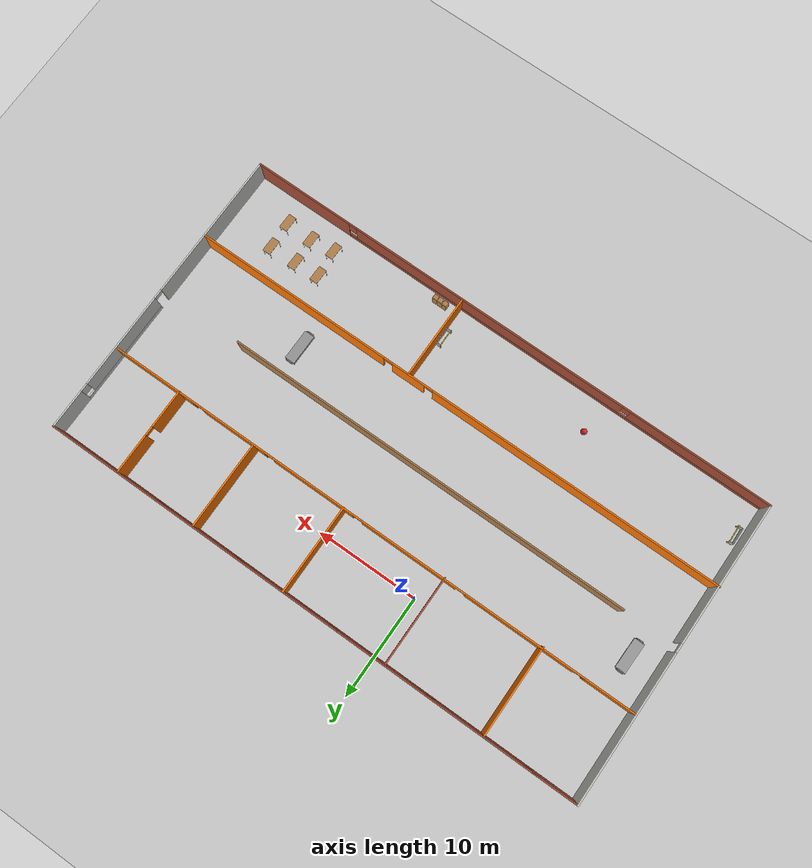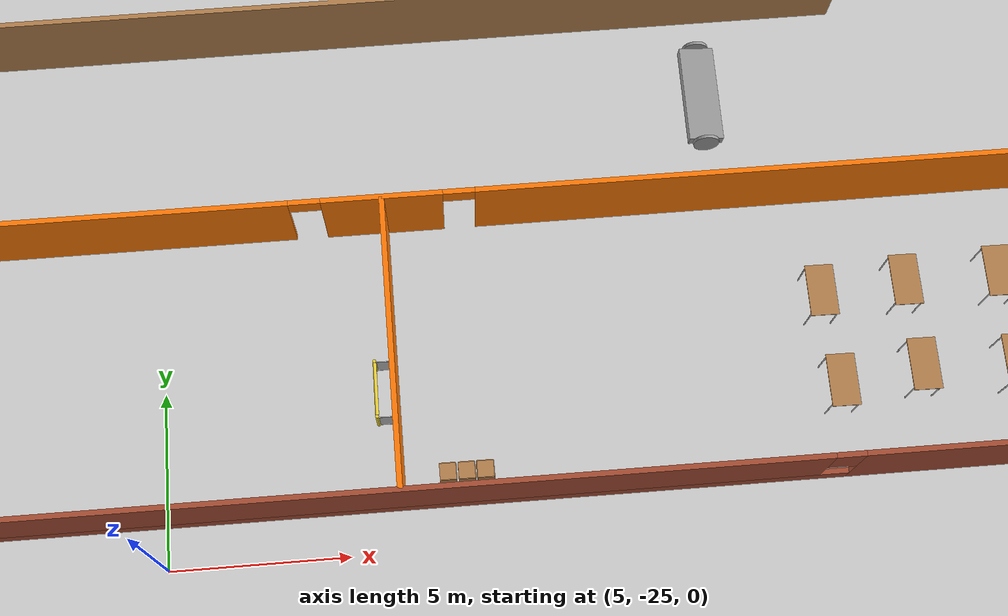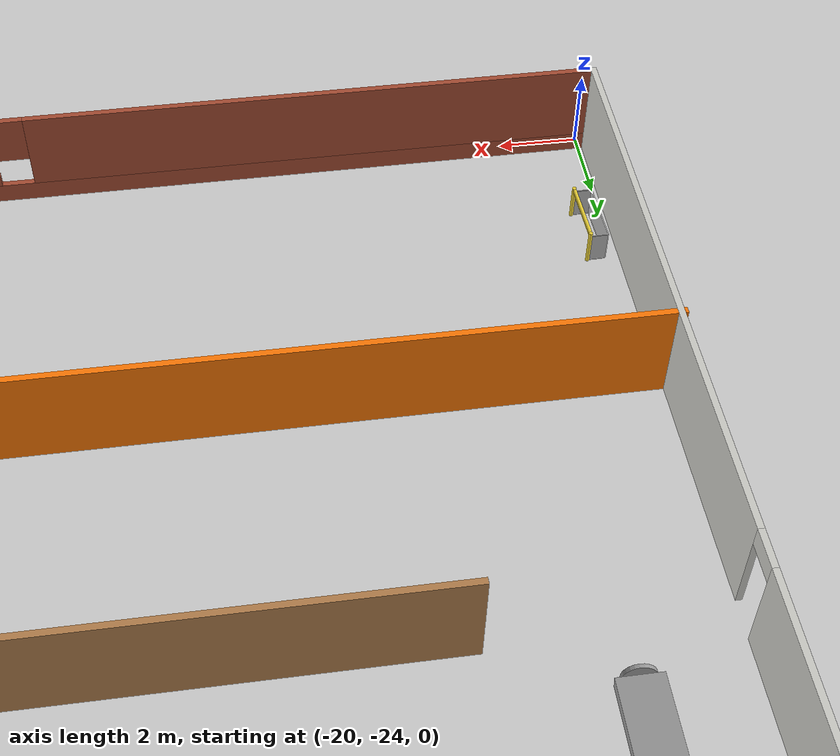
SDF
<sdf version="1.6">
 <world name="default">
  <plugin name="hello" filename="libhello.so"/>
  <light name="sun" type="directional">
   <pose>0 0 10 0 -0 0</pose>
   <diffuse>0.8 0.8 0.8 1</diffuse>
   <specular>0.2 0.2 0.2 1</specular>
   <attenuation>
    <range>1000</range>
    <constant>0.9</constant>
    <linear>0.01</linear>
    <quadratic>0.001</quadratic>
   </attenuation>
   <direction>-0.5 0.1 -0.9</direction>
  </light>
  <model name="ground_plane">
   <static>1</static>
   <link name="link">
    <collision name="collision">
     <geometry><plane><normal>0 0 1</normal><size>100 100</size></plane></geometry>
     <surface>
      <contact><collide_bitmask>65535</collide_bitmask></contact>
      <friction><ode><mu>100</mu><mu2>50</mu2></ode></friction>
     </surface>
    </collision>
    <visual name="visual">
     <cast_shadows>0</cast_shadows>
     <geometry><plane><normal>0 0 1</normal><size>100 100</size></plane></geometry>
     <material>
      <script><uri>file://media/materials/scripts/gazebo.material</uri><name>Gazebo/Grey</name></script>
     </material>
    </visual>
   </link>
  </model>
  <gravity>0 0 -9.8</gravity>
  <magnetic_field>6e-06 2.3e-05 -4.2e-05</magnetic_field>
  <atmosphere type="adiabatic"/>
  <physics name="default_physics" default="0" type="ode">
   <max_step_size>0.001</max_step_size>
   <real_time_factor>1</real_time_factor>
   <real_time_update_rate>1000</real_time_update_rate>
  </physics>
  <scene><ambient>0.4 0.4 0.4 1</ambient><background>0.7 0.7 0.7 1</background><shadows>1</shadows></scene>
  <spherical_coordinates>
   <surface_model>EARTH_WGS84</surface_model>
   <latitude_deg>0</latitude_deg>
   <longitude_deg>0</longitude_deg>
   <elevation>0</elevation>
   <heading_deg>0</heading_deg>
  </spherical_coordinates>
  <model name="building">
   <pose>6.75578 -8.9413 0 0 -0 0</pose>
   <link name="Wall_63">
    <pose>0.95692 14.8001 0 0 -0 0</pose>
    <visual name="Wall_63_Visual_0">
     <pose>-24.8797 0 1.25 0 -0 0</pose>
     <geometry><box><size>2.49063 0.15 2.5</size></box></geometry>
     <material>
      <script><uri>file://media/materials/scripts/gazebo.material</uri><name>Gazebo/Bricks</name></script>
      <ambient>1 0.764706 0.305882 1</ambient>
     </material>
     <meta><layer>0</layer></meta>
    </visual>
    <collision name="Wall_63_Collision_0">
     <geometry><box><size>2.49063 0.15 2.5</size></box></geometry>
     <pose>-24.8797 0 1.25 0 -0 0</pose>
    </collision>
    <visual name="Wall_63_Visual_1">
     <pose>1.24532 0 0.25 0 -0 0</pose>
     <geometry><box><size>49.7594 0.15 0.5</size></box></geometry>
     <material>
      <script><uri>file://media/materials/scripts/gazebo.material</uri><name>Gazebo/Bricks</name></script>
      <ambient>1 0.764706 0.305882 1</ambient>
     </material>
     <meta><layer>0</layer></meta>
    </visual>
    <collision name="Wall_63_Collision_1">
     <geometry><box><size>49.7594 0.15 0.5</size></box></geometry>
     <pose>1.24532 0 0.25 0 -0 0</pose>
    </collision>
    <visual name="Wall_63_Visual_2">
     <pose>-18.3114 0 1.5 0 -0 0</pose>
     <geometry><box><size>9.04584 0.15 2</size></box></geometry>
     <material>
      <script><uri>file://media/materials/scripts/gazebo.material</uri><name>Gazebo/Bricks</name></script>
      <ambient>1 0.764706 0.305882 1</ambient>
     </material>
     <meta><layer>0</layer></meta>
    </visual>
    <collision name="Wall_63_Collision_2">
     <geometry><box><size>9.04584 0.15 2</size></box></geometry>
     <pose>-18.3114 0 1.5 0 -0 0</pose>
    </collision>
    <visual name="Wall_63_Visual_3">
     <pose>-8.50629 0 1.5 0 -0 0</pose>
     <geometry><box><size>8.96447 0.15 2</size></box></geometry>
     <material>
      <script><uri>file://media/materials/scripts/gazebo.material</uri><name>Gazebo/Bricks</name></script>
      <ambient>1 0.764706 0.305882 1</ambient>
     </material>
     <meta><layer>0</layer></meta>
    </visual>
    <collision name="Wall_63_Collision_3">
     <geometry><box><size>8.96447 0.15 2</size></box></geometry>
     <pose>-8.50629 0 1.5 0 -0 0</pose>
    </collision>
    <visual name="Wall_63_Visual_4">
     <pose>1.29887 0 1.5 0 -0 0</pose>
     <geometry><box><size>9.04584 0.15 2</size></box></geometry>
     <material>
      <script><uri>file://media/materials/scripts/gazebo.material</uri><name>Gazebo/Bricks</name></script>
      <ambient>1 0.764706 0.305882 1</ambient>
     </material>
     <meta><layer>0</layer></meta>
    </visual>
    <collision name="Wall_63_Collision_4">
     <geometry><box><size>9.04584 0.15 2</size></box></geometry>
     <pose>1.29887 0 1.5 0 -0 0</pose>
    </collision>
    <visual name="Wall_63_Visual_5">
     <pose>10.3717 0 1.5 0 -0 0</pose>
     <geometry><box><size>7.4998 0.15 2</size></box></geometry>
     <material>
      <script><uri>file://media/materials/scripts/gazebo.material</uri><name>Gazebo/Bricks</name></script>
      <ambient>1 0.764706 0.305882 1</ambient>
     </material>
     <meta><layer>0</layer></meta>
    </visual>
    <collision name="Wall_63_Collision_5">
     <geometry><box><size>7.4998 0.15 2</size></box></geometry>
     <pose>10.3717 0 1.5 0 -0 0</pose>
    </collision>
    <visual name="Wall_63_Visual_6">
     <pose>20.5233 0 1.5 0 -0 0</pose>
     <geometry><box><size>11.2034 0.15 2</size></box></geometry>
     <material>
      <script><uri>file://media/materials/scripts/gazebo.material</uri><name>Gazebo/Bricks</name></script>
      <ambient>1 0.764706 0.305882 1</ambient>
     </material>
     <meta><layer>0</layer></meta>
    </visual>
    <collision name="Wall_63_Collision_6">
     <geometry><box><size>11.2034 0.15 2</size></box></geometry>
     <pose>20.5233 0 1.5 0 -0 0</pose>
    </collision>
    <visual name="Wall_63_Visual_7">
     <pose>-23.2344 0 1.9 0 -0 0</pose>
     <geometry><box><size>0.8 0.15 1.2</size></box></geometry>
     <material>
      <script><uri>file://media/materials/scripts/gazebo.material</uri><name>Gazebo/Bricks</name></script>
      <ambient>1 0.764706 0.305882 1</ambient>
     </material>
     <meta><layer>0</layer></meta>
    </visual>
    <collision name="Wall_63_Collision_7">
     <geometry><box><size>0.8 0.15 1.2</size></box></geometry>
     <pose>-23.2344 0 1.9 0 -0 0</pose>
    </collision>
    <visual name="Wall_63_Visual_8">
     <pose>-13.3885 0 1.9 0 -0 0</pose>
     <geometry><box><size>0.8 0.15 1.2</size></box></geometry>
     <material>
      <script><uri>file://media/materials/scripts/gazebo.material</uri><name>Gazebo/Bricks</name></script>
      <ambient>1 0.764706 0.305882 1</ambient>
     </material>
     <meta><layer>0</layer></meta>
    </visual>
    <collision name="Wall_63_Collision_8">
     <geometry><box><size>0.8 0.15 1.2</size></box></geometry>
     <pose>-13.3885 0 1.9 0 -0 0</pose>
    </collision>
    <visual name="Wall_63_Visual_9">
     <pose>-3.62405 0 1.9 0 -0 0</pose>
     <geometry><box><size>0.8 0.15 1.2</size></box></geometry>
     <material>
      <script><uri>file://media/materials/scripts/gazebo.material</uri><name>Gazebo/Bricks</name></script>
      <ambient>1 0.764706 0.305882 1</ambient>
     </material>
     <meta><layer>0</layer></meta>
    </visual>
    <collision name="Wall_63_Collision_9">
     <geometry><box><size>0.8 0.15 1.2</size></box></geometry>
     <pose>-3.62405 0 1.9 0 -0 0</pose>
    </collision>
    <visual name="Wall_63_Visual_10">
     <pose>6.2218 0 1.9 0 -0 0</pose>
     <geometry><box><size>0.8 0.15 1.2</size></box></geometry>
     <material>
      <script><uri>file://media/materials/scripts/gazebo.material</uri><name>Gazebo/Bricks</name></script>
      <ambient>1 0.764706 0.305882 1</ambient>
     </material>
     <meta><layer>0</layer></meta>
    </visual>
    <collision name="Wall_63_Collision_10">
     <geometry><box><size>0.8 0.15 1.2</size></box></geometry>
     <pose>6.2218 0 1.9 0 -0 0</pose>
    </collision>
    <visual name="Wall_63_Visual_11">
     <pose>14.5216 0 1.9 0 -0 0</pose>
     <geometry><box><size>0.8 0.15 1.2</size></box></geometry>
     <material>
      <script><uri>file://media/materials/scripts/gazebo.material</uri><name>Gazebo/Bricks</name></script>
      <ambient>1 0.764706 0.305882 1</ambient>
     </material>
     <meta><layer>0</layer></meta>
    </visual>
    <collision name="Wall_63_Collision_11">
     <geometry><box><size>0.8 0.15 1.2</size></box></geometry>
     <pose>14.5216 0 1.9 0 -0 0</pose>
    </collision>
   </link>
   <link name="Wall_64">
    <pose>26.9601 -0.04667 0 0 0 -1.57397</pose>
    <visual name="Wall_64_Visual_0">
     <pose>-12.9387 0 1.25 0 -0 0</pose>
     <geometry><box><size>3.77926 0.15 2.5</size></box></geometry>
     <material>
      <script><uri>file://media/materials/scripts/gazebo.material</uri><name>Gazebo/CeilingTiled</name></script>
      <ambient>0.996078 0.47451 0.0196078 1</ambient>
     </material>
     <meta><layer>0</layer></meta>
    </visual>
    <collision name="Wall_64_Collision_0">
     <geometry><box><size>3.77926 0.15 2.5</size></box></geometry>
     <pose>-12.9387 0 1.25 0 -0 0</pose>
    </collision>
    <visual name="Wall_64_Visual_1">
     <pose>7.50603 0 1.25 0 -0 0</pose>
     <geometry><box><size>14.6445 0.15 2.5</size></box></geometry>
     <material>
      <script><uri>file://media/materials/scripts/gazebo.material</uri><name>Gazebo/CeilingTiled</name></script>
      <ambient>0.996078 0.47451 0.0196078 1</ambient>
     </material>
     <meta><layer>0</layer></meta>
    </visual>
    <collision name="Wall_64_Collision_1">
     <geometry><box><size>14.6445 0.15 2.5</size></box></geometry>
     <pose>7.50603 0 1.25 0 -0 0</pose>
    </collision>
    <visual name="Wall_64_Visual_2">
     <pose>-5.88262 0 0.25 0 -0 0</pose>
     <geometry><box><size>10.3328 0.15 0.5</size></box></geometry>
     <material>
      <script><uri>file://media/materials/scripts/gazebo.material</uri><name>Gazebo/CeilingTiled</name></script>
      <ambient>0.996078 0.47451 0.0196078 1</ambient>
     </material>
     <meta><layer>0</layer></meta>
    </visual>
    <collision name="Wall_64_Collision_2">
     <geometry><box><size>10.3328 0.15 0.5</size></box></geometry>
     <pose>-5.88262 0 0.25 0 -0 0</pose>
    </collision>
    <visual name="Wall_64_Visual_3">
     <pose>-5.48262 0 1.5 0 -0 0</pose>
     <geometry><box><size>9.5328 0.15 2</size></box></geometry>
     <material>
      <script><uri>file://media/materials/scripts/gazebo.material</uri><name>Gazebo/CeilingTiled</name></script>
      <ambient>0.996078 0.47451 0.0196078 1</ambient>
     </material>
     <meta><layer>0</layer></meta>
    </visual>
    <collision name="Wall_64_Collision_3">
     <geometry><box><size>9.5328 0.15 2</size></box></geometry>
     <pose>-5.48262 0 1.5 0 -0 0</pose>
    </collision>
    <visual name="Wall_64_Visual_4">
     <pose>-10.649 0 1.9 0 -0 0</pose>
     <geometry><box><size>0.8 0.15 1.2</size></box></geometry>
     <material>
      <script><uri>file://media/materials/scripts/gazebo.material</uri><name>Gazebo/CeilingTiled</name></script>
      <ambient>0.996078 0.47451 0.0196078 1</ambient>
     </material>
     <meta><layer>0</layer></meta>
    </visual>
    <collision name="Wall_64_Collision_4">
     <geometry><box><size>0.8 0.15 1.2</size></box></geometry>
     <pose>-10.649 0 1.9 0 -0 0</pose>
    </collision>
    <visual name="Wall_64_Visual_5">
     <pose>-0.266225 0 2.25 0 -0 0</pose>
     <geometry><box><size>0.9 0.15 0.5</size></box></geometry>
     <material>
      <script><uri>file://media/materials/scripts/gazebo.material</uri><name>Gazebo/CeilingTiled</name></script>
      <ambient>0.996078 0.47451 0.0196078 1</ambient>
     </material>
     <meta><layer>0</layer></meta>
    </visual>
    <collision name="Wall_64_Collision_5">
     <geometry><box><size>0.9 0.15 0.5</size></box></geometry>
     <pose>-0.266225 0 2.25 0 -0 0</pose>
    </collision>
   </link>
   <link name="Wall_65">
    <pose>-0.011657 -14.7999 0 0 -0 3.14159</pose>
    <visual name="Wall_65_Visual_0">
     <pose>-22.0191 0 1.25 0 -0 0</pose>
     <geometry><box><size>9.96181 0.15 2.5</size></box></geometry>
     <material>
      <script><uri>file://media/materials/scripts/gazebo.material</uri><name>Gazebo/Bricks</name></script>
      <ambient>1 0.764706 0.305882 1</ambient>
     </material>
     <meta><layer>0</layer></meta>
    </visual>
    <collision name="Wall_65_Collision_0">
     <geometry><box><size>9.96181 0.15 2.5</size></box></geometry>
     <pose>-22.0191 0 1.25 0 -0 0</pose>
    </collision>
    <visual name="Wall_65_Visual_1">
     <pose>4.9809 0 0.25 0 -0 0</pose>
     <geometry><box><size>44.0382 0.15 0.5</size></box></geometry>
     <material>
      <script><uri>file://media/materials/scripts/gazebo.material</uri><name>Gazebo/Bricks</name></script>
      <ambient>1 0.764706 0.305882 1</ambient>
     </material>
     <meta><layer>0</layer></meta>
    </visual>
    <collision name="Wall_65_Collision_1">
     <geometry><box><size>44.0382 0.15 0.5</size></box></geometry>
     <pose>4.9809 0 0.25 0 -0 0</pose>
    </collision>
    <visual name="Wall_65_Visual_2">
     <pose>-2.08709 0 1.5 0 -0 0</pose>
     <geometry><box><size>28.3022 0.15 2</size></box></geometry>
     <material>
      <script><uri>file://media/materials/scripts/gazebo.material</uri><name>Gazebo/Bricks</name></script>
      <ambient>1 0.764706 0.305882 1</ambient>
     </material>
     <meta><layer>0</layer></meta>
    </visual>
    <collision name="Wall_65_Collision_2">
     <geometry><box><size>28.3022 0.15 2</size></box></geometry>
     <pose>-2.08709 0 1.5 0 -0 0</pose>
    </collision>
    <visual name="Wall_65_Visual_3">
     <pose>19.932 0 1.5 0 -0 0</pose>
     <geometry><box><size>14.136 0.15 2</size></box></geometry>
     <material>
      <script><uri>file://media/materials/scripts/gazebo.material</uri><name>Gazebo/Bricks</name></script>
      <ambient>1 0.764706 0.305882 1</ambient>
     </material>
     <meta><layer>0</layer></meta>
    </visual>
    <collision name="Wall_65_Collision_3">
     <geometry><box><size>14.136 0.15 2</size></box></geometry>
     <pose>19.932 0 1.5 0 -0 0</pose>
    </collision>
    <visual name="Wall_65_Visual_4">
     <pose>-16.6382 0 1.9 0 -0 0</pose>
     <geometry><box><size>0.8 0.15 1.2</size></box></geometry>
     <material>
      <script><uri>file://media/materials/scripts/gazebo.material</uri><name>Gazebo/Bricks</name></script>
      <ambient>1 0.764706 0.305882 1</ambient>
     </material>
     <meta><layer>0</layer></meta>
    </visual>
    <collision name="Wall_65_Collision_4">
     <geometry><box><size>0.8 0.15 1.2</size></box></geometry>
     <pose>-16.6382 0 1.9 0 -0 0</pose>
    </collision>
    <visual name="Wall_65_Visual_5">
     <pose>12.464 0 1.9 0 -0 0</pose>
     <geometry><box><size>0.8 0.15 1.2</size></box></geometry>
     <material>
      <script><uri>file://media/materials/scripts/gazebo.material</uri><name>Gazebo/Bricks</name></script>
      <ambient>1 0.764706 0.305882 1</ambient>
     </material>
     <meta><layer>0</layer></meta>
    </visual>
    <collision name="Wall_65_Collision_5">
     <geometry><box><size>0.8 0.15 1.2</size></box></geometry>
     <pose>12.464 0 1.9 0 -0 0</pose>
    </collision>
   </link>
   <link name="Wall_66">
    <pose>-26.9367 0.000119 0 0 -0 1.5708</pose>
    <visual name="Wall_66_Visual_0">
     <pose>-7.83319 0 1.25 0 -0 0</pose>
     <geometry><box><size>14.0836 0.15 2.5</size></box></geometry>
     <material>
      <script><uri>file://media/materials/scripts/gazebo.material</uri><name>Gazebo/CeilingTiled</name></script>
      <ambient>0.996078 0.47451 0.0196078 1</ambient>
     </material>
     <meta><layer>0</layer></meta>
    </visual>
    <collision name="Wall_66_Collision_0">
     <geometry><box><size>14.0836 0.15 2.5</size></box></geometry>
     <pose>-7.83319 0 1.25 0 -0 0</pose>
    </collision>
    <visual name="Wall_66_Visual_1">
     <pose>7.49181 0 1.25 0 -0 0</pose>
     <geometry><box><size>14.7664 0.15 2.5</size></box></geometry>
     <material>
      <script><uri>file://media/materials/scripts/gazebo.material</uri><name>Gazebo/CeilingTiled</name></script>
      <ambient>0.996078 0.47451 0.0196078 1</ambient>
     </material>
     <meta><layer>0</layer></meta>
    </visual>
    <collision name="Wall_66_Collision_1">
     <geometry><box><size>14.7664 0.15 2.5</size></box></geometry>
     <pose>7.49181 0 1.25 0 -0 0</pose>
    </collision>
    <visual name="Wall_66_Visual_2">
     <pose>-0.341387 0 2.25 0 -0 0</pose>
     <geometry><box><size>0.9 0.15 0.5</size></box></geometry>
     <material>
      <script><uri>file://media/materials/scripts/gazebo.material</uri><name>Gazebo/CeilingTiled</name></script>
      <ambient>0.996078 0.47451 0.0196078 1</ambient>
     </material>
     <meta><layer>0</layer></meta>
    </visual>
    <collision name="Wall_66_Collision_2">
     <geometry><box><size>0.9 0.15 0.5</size></box></geometry>
     <pose>-0.341387 0 2.25 0 -0 0</pose>
    </collision>
   </link>
   <link name="Wall_67">
    <collision name="Wall_67_Collision">
     <geometry><box><size>4.5 0.15 2.5</size></box></geometry>
     <pose>0 0 1.25 0 -0 0</pose>
    </collision>
    <visual name="Wall_67_Visual">
     <pose>0 0 1.25 0 -0 0</pose>
     <geometry><box><size>4.5 0.15 2.5</size></box></geometry>
     <material>
      <script><uri>file://media/materials/scripts/gazebo.material</uri><name>Gazebo/Bricks</name></script>
      <ambient>1 0.764706 0.305882 1</ambient>
     </material>
     <meta><layer>0</layer></meta>
    </visual>
    <pose>-24.7617 14.8001 0 0 -0 0</pose>
   </link>
   <link name="Wall_69">
    <pose>-0.045335 6.18308 0 0 -0 0</pose>
    <visual name="Wall_69_Visual_0">
     <pose>-24.4109 0 1.25 0 -0 0</pose>
     <geometry><box><size>4.92813 0.15 2.5</size></box></geometry>
     <material>
      <script><uri>file://media/materials/scripts/gazebo.material</uri><name>Gazebo/Grey</name></script>
      <ambient>0.996078 0.47451 0.0196078 1</ambient>
     </material>
     <meta><layer>0</layer></meta>
    </visual>
    <collision name="Wall_69_Collision_0">
     <geometry><box><size>4.92813 0.15 2.5</size></box></geometry>
     <pose>-24.4109 0 1.25 0 -0 0</pose>
    </collision>
    <visual name="Wall_69_Visual_1">
     <pose>-15.5239 0 1.25 0 -0 0</pose>
     <geometry><box><size>11.046 0.15 2.5</size></box></geometry>
     <material>
      <script><uri>file://media/materials/scripts/gazebo.material</uri><name>Gazebo/Grey</name></script>
      <ambient>0.996078 0.47451 0.0196078 1</ambient>
     </material>
     <meta><layer>0</layer></meta>
    </visual>
    <collision name="Wall_69_Collision_1">
     <geometry><box><size>11.046 0.15 2.5</size></box></geometry>
     <pose>-15.5239 0 1.25 0 -0 0</pose>
    </collision>
    <visual name="Wall_69_Visual_2">
     <pose>-4.21424 0 1.25 0 -0 0</pose>
     <geometry><box><size>9.77329 0.15 2.5</size></box></geometry>
     <material>
      <script><uri>file://media/materials/scripts/gazebo.material</uri><name>Gazebo/Grey</name></script>
      <ambient>0.996078 0.47451 0.0196078 1</ambient>
     </material>
     <meta><layer>0</layer></meta>
    </visual>
    <collision name="Wall_69_Collision_2">
     <geometry><box><size>9.77329 0.15 2.5</size></box></geometry>
     <pose>-4.21424 0 1.25 0 -0 0</pose>
    </collision>
    <visual name="Wall_69_Visual_3">
     <pose>5.78359 0 1.25 0 -0 0</pose>
     <geometry><box><size>8.42237 0.15 2.5</size></box></geometry>
     <material>
      <script><uri>file://media/materials/scripts/gazebo.material</uri><name>Gazebo/Grey</name></script>
      <ambient>0.996078 0.47451 0.0196078 1</ambient>
     </material>
     <meta><layer>0</layer></meta>
    </visual>
    <collision name="Wall_69_Collision_3">
     <geometry><box><size>8.42237 0.15 2.5</size></box></geometry>
     <pose>5.78359 0 1.25 0 -0 0</pose>
    </collision>
    <visual name="Wall_69_Visual_4">
     <pose>14.3144 0 1.25 0 -0 0</pose>
     <geometry><box><size>6.83933 0.15 2.5</size></box></geometry>
     <material>
      <script><uri>file://media/materials/scripts/gazebo.material</uri><name>Gazebo/Grey</name></script>
      <ambient>0.996078 0.47451 0.0196078 1</ambient>
     </material>
     <meta><layer>0</layer></meta>
    </visual>
    <collision name="Wall_69_Collision_4">
     <geometry><box><size>6.83933 0.15 2.5</size></box></geometry>
     <pose>14.3144 0 1.25 0 -0 0</pose>
    </collision>
    <visual name="Wall_69_Visual_5">
     <pose>22.7546 0 1.25 0 -0 0</pose>
     <geometry><box><size>8.2409 0.15 2.5</size></box></geometry>
     <material>
      <script><uri>file://media/materials/scripts/gazebo.material</uri><name>Gazebo/Grey</name></script>
      <ambient>0.996078 0.47451 0.0196078 1</ambient>
     </material>
     <meta><layer>0</layer></meta>
    </visual>
    <collision name="Wall_69_Collision_5">
     <geometry><box><size>8.2409 0.15 2.5</size></box></geometry>
     <pose>22.7546 0 1.25 0 -0 0</pose>
    </collision>
    <visual name="Wall_69_Visual_6">
     <pose>-21.4969 0 2.25 0 -0 0</pose>
     <geometry><box><size>0.9 0.15 0.5</size></box></geometry>
     <material>
      <script><uri>file://media/materials/scripts/gazebo.material</uri><name>Gazebo/Grey</name></script>
      <ambient>0.996078 0.47451 0.0196078 1</ambient>
     </material>
     <meta><layer>0</layer></meta>
    </visual>
    <collision name="Wall_69_Collision_6">
     <geometry><box><size>0.9 0.15 0.5</size></box></geometry>
     <pose>-21.4969 0 2.25 0 -0 0</pose>
    </collision>
    <visual name="Wall_69_Visual_7">
     <pose>-9.55089 0 2.25 0 -0 0</pose>
     <geometry><box><size>0.9 0.15 0.5</size></box></geometry>
     <material>
      <script><uri>file://media/materials/scripts/gazebo.material</uri><name>Gazebo/Grey</name></script>
      <ambient>0.996078 0.47451 0.0196078 1</ambient>
     </material>
     <meta><layer>0</layer></meta>
    </visual>
    <collision name="Wall_69_Collision_7">
     <geometry><box><size>0.9 0.15 0.5</size></box></geometry>
     <pose>-9.55089 0 2.25 0 -0 0</pose>
    </collision>
    <visual name="Wall_69_Visual_8">
     <pose>1.12241 0 2.25 0 -0 0</pose>
     <geometry><box><size>0.9 0.15 0.5</size></box></geometry>
     <material>
      <script><uri>file://media/materials/scripts/gazebo.material</uri><name>Gazebo/Grey</name></script>
      <ambient>0.996078 0.47451 0.0196078 1</ambient>
     </material>
     <meta><layer>0</layer></meta>
    </visual>
    <collision name="Wall_69_Collision_8">
     <geometry><box><size>0.9 0.15 0.5</size></box></geometry>
     <pose>1.12241 0 2.25 0 -0 0</pose>
    </collision>
    <visual name="Wall_69_Visual_9">
     <pose>10.4448 0 2.25 0 -0 0</pose>
     <geometry><box><size>0.9 0.15 0.5</size></box></geometry>
     <material>
      <script><uri>file://media/materials/scripts/gazebo.material</uri><name>Gazebo/Grey</name></script>
      <ambient>0.996078 0.47451 0.0196078 1</ambient>
     </material>
     <meta><layer>0</layer></meta>
    </visual>
    <collision name="Wall_69_Collision_9">
     <geometry><box><size>0.9 0.15 0.5</size></box></geometry>
     <pose>10.4448 0 2.25 0 -0 0</pose>
    </collision>
    <visual name="Wall_69_Visual_10">
     <pose>18.1841 0 2.25 0 -0 0</pose>
     <geometry><box><size>0.9 0.15 0.5</size></box></geometry>
     <material>
      <script><uri>file://media/materials/scripts/gazebo.material</uri><name>Gazebo/Grey</name></script>
      <ambient>0.996078 0.47451 0.0196078 1</ambient>
     </material>
     <meta><layer>0</layer></meta>
    </visual>
    <collision name="Wall_69_Collision_10">
     <geometry><box><size>0.9 0.15 0.5</size></box></geometry>
     <pose>18.1841 0 2.25 0 -0 0</pose>
    </collision>
   </link>
   <link name="Wall_71">
    <pose>-0.082157 -6.51997 0 0 -0 0</pose>
    <visual name="Wall_71_Visual_0">
     <pose>-12.3837 0 1.25 0 -0 0</pose>
     <geometry><box><size>29.2326 0.15 2.5</size></box></geometry>
     <material>
      <script><uri>file://media/materials/scripts/gazebo.material</uri><name>Gazebo/Grey</name></script>
      <ambient>0.996078 0.47451 0.0196078 1</ambient>
     </material>
     <meta><layer>0</layer></meta>
    </visual>
    <collision name="Wall_71_Collision_0">
     <geometry><box><size>29.2326 0.15 2.5</size></box></geometry>
     <pose>-12.3837 0 1.25 0 -0 0</pose>
    </collision>
    <visual name="Wall_71_Visual_1">
     <pose>4.83487 0 1.25 0 -0 0</pose>
     <geometry><box><size>3.4045 0.15 2.5</size></box></geometry>
     <material>
      <script><uri>file://media/materials/scripts/gazebo.material</uri><name>Gazebo/Grey</name></script>
      <ambient>0.996078 0.47451 0.0196078 1</ambient>
     </material>
     <meta><layer>0</layer></meta>
    </visual>
    <collision name="Wall_71_Collision_1">
     <geometry><box><size>3.4045 0.15 2.5</size></box></geometry>
     <pose>4.83487 0 1.25 0 -0 0</pose>
    </collision>
    <visual name="Wall_71_Visual_2">
     <pose>17.2186 0 1.25 0 -0 0</pose>
     <geometry><box><size>19.5629 0.15 2.5</size></box></geometry>
     <material>
      <script><uri>file://media/materials/scripts/gazebo.material</uri><name>Gazebo/Grey</name></script>
      <ambient>0.996078 0.47451 0.0196078 1</ambient>
     </material>
     <meta><layer>0</layer></meta>
    </visual>
    <collision name="Wall_71_Collision_2">
     <geometry><box><size>19.5629 0.15 2.5</size></box></geometry>
     <pose>17.2186 0 1.25 0 -0 0</pose>
    </collision>
    <visual name="Wall_71_Visual_3">
     <pose>2.68262 0 2.25 0 -0 0</pose>
     <geometry><box><size>0.9 0.15 0.5</size></box></geometry>
     <material>
      <script><uri>file://media/materials/scripts/gazebo.material</uri><name>Gazebo/Grey</name></script>
      <ambient>0.996078 0.47451 0.0196078 1</ambient>
     </material>
     <meta><layer>0</layer></meta>
    </visual>
    <collision name="Wall_71_Collision_3">
     <geometry><box><size>0.9 0.15 0.5</size></box></geometry>
     <pose>2.68262 0 2.25 0 -0 0</pose>
    </collision>
    <visual name="Wall_71_Visual_4">
     <pose>6.98712 0 2.25 0 -0 0</pose>
     <geometry><box><size>0.9 0.15 0.5</size></box></geometry>
     <material>
      <script><uri>file://media/materials/scripts/gazebo.material</uri><name>Gazebo/Grey</name></script>
      <ambient>0.996078 0.47451 0.0196078 1</ambient>
     </material>
     <meta><layer>0</layer></meta>
    </visual>
    <collision name="Wall_71_Collision_4">
     <geometry><box><size>0.9 0.15 0.5</size></box></geometry>
     <pose>6.98712 0 2.25 0 -0 0</pose>
    </collision>
   </link>
   <link name="Wall_73">
    <collision name="Wall_73_Collision">
     <geometry><box><size>8.75 0.15 2.5</size></box></geometry>
     <pose>0 0 1.25 0 -0 0</pose>
    </collision>
    <visual name="Wall_73_Visual">
     <pose>0 0 1.25 0 -0 0</pose>
     <geometry><box><size>8.75 0.15 2.5</size></box></geometry>
     <material>
      <script><uri>file://media/materials/scripts/gazebo.material</uri><name>Gazebo/Grey</name></script>
      <ambient>0.996078 0.47451 0.0196078 1</ambient>
     </material>
     <meta><layer>0</layer></meta>
    </visual>
    <pose>-17.7428 10.3617 0 0 -0 1.5708</pose>
   </link>
   <link name="Wall_75">
    <collision name="Wall_75_Collision">
     <geometry><box><size>8.75 0.15 2.5</size></box></geometry>
     <pose>0 0 1.25 0 -0 0</pose>
    </collision>
    <visual name="Wall_75_Visual">
     <pose>0 0 1.25 0 -0 0</pose>
     <geometry><box><size>8.75 0.15 2.5</size></box></geometry>
     <material>
      <script><uri>file://media/materials/scripts/gazebo.material</uri><name>Gazebo/Bricks</name></script>
      <ambient>0.996078 0.47451 0.0196078 1</ambient>
     </material>
     <meta><layer>0</layer></meta>
    </visual>
    <pose>-7.87167 10.3788 0 0 0 -1.5708</pose>
   </link>
   <link name="Wall_77">
    <collision name="Wall_77_Collision">
     <geometry><box><size>8.75 0.15 2.5</size></box></geometry>
     <pose>0 0 1.25 0 -0 0</pose>
    </collision>
    <visual name="Wall_77_Visual">
     <pose>0 0 1.25 0 -0 0</pose>
     <geometry><box><size>8.75 0.15 2.5</size></box></geometry>
     <material>
      <script><uri>file://media/materials/scripts/gazebo.material</uri><name>Gazebo/Grey</name></script>
      <ambient>0.996078 0.47451 0.0196078 1</ambient>
     </material>
     <meta><layer>0</layer></meta>
    </visual>
    <pose>2.52541 10.4597 0 0 0 -1.5708</pose>
   </link>
   <link name="Wall_79">
    <collision name="Wall_79_Collision">
     <geometry><box><size>8.5 0.15 2.5</size></box></geometry>
     <pose>0 0 1.25 0 -0 0</pose>
    </collision>
    <visual name="Wall_79_Visual">
     <pose>0 0 1.25 0 -0 0</pose>
     <geometry><box><size>8.5 0.15 2.5</size></box></geometry>
     <material>
      <script><uri>file://media/materials/scripts/gazebo.material</uri><name>Gazebo/Grey</name></script>
      <ambient>0.996078 0.47451 0.0196078 1</ambient>
     </material>
     <meta><layer>0</layer></meta>
    </visual>
    <pose>11.992 10.5038 0 0 0 -1.5708</pose>
   </link>
   <link name="Wall_81">
    <pose>20.0427 10.4597 0 0 0 -1.5708</pose>
    <visual name="Wall_81_Visual_0">
     <pose>-2.38459 0 1.25 0 -0 0</pose>
     <geometry><box><size>3.98082 0.15 2.5</size></box></geometry>
     <material>
      <script><uri>file://media/materials/scripts/gazebo.material</uri><name>Gazebo/Grey</name></script>
      <ambient>0.996078 0.47451 0.0196078 1</ambient>
     </material>
     <meta><layer>0</layer></meta>
    </visual>
    <collision name="Wall_81_Collision_0">
     <geometry><box><size>3.98082 0.15 2.5</size></box></geometry>
     <pose>-2.38459 0 1.25 0 -0 0</pose>
    </collision>
    <visual name="Wall_81_Visual_1">
     <pose>2.44041 0 1.25 0 -0 0</pose>
     <geometry><box><size>3.86918 0.15 2.5</size></box></geometry>
     <material>
      <script><uri>file://media/materials/scripts/gazebo.material</uri><name>Gazebo/Grey</name></script>
      <ambient>0.996078 0.47451 0.0196078 1</ambient>
     </material>
     <meta><layer>0</layer></meta>
    </visual>
    <collision name="Wall_81_Collision_1">
     <geometry><box><size>3.86918 0.15 2.5</size></box></geometry>
     <pose>2.44041 0 1.25 0 -0 0</pose>
    </collision>
    <visual name="Wall_81_Visual_2">
     <pose>0.055823 0 2.25 0 -0 0</pose>
     <geometry><box><size>0.9 0.15 0.5</size></box></geometry>
     <material>
      <script><uri>file://media/materials/scripts/gazebo.material</uri><name>Gazebo/Grey</name></script>
      <ambient>0.996078 0.47451 0.0196078 1</ambient>
     </material>
     <meta><layer>0</layer></meta>
    </visual>
    <collision name="Wall_81_Collision_2">
     <geometry><box><size>0.9 0.15 0.5</size></box></geometry>
     <pose>0.055823 0 2.25 0 -0 0</pose>
    </collision>
   </link>
   <link name="Wall_83">
    <collision name="Wall_83_Collision">
     <geometry><box><size>8.25 0.15 2.5</size></box></geometry>
     <pose>0 0 1.25 0 -0 0</pose>
    </collision>
    <visual name="Wall_83_Visual">
     <pose>0 0 1.25 0 -0 0</pose>
     <geometry><box><size>8.25 0.15 2.5</size></box></geometry>
     <material>
      <script><uri>file://media/materials/scripts/gazebo.material</uri><name>Gazebo/Grey</name></script>
      <ambient>0.996078 0.47451 0.0196078 1</ambient>
     </material>
     <meta><layer>0</layer></meta>
    </visual>
    <pose>4.75047 -10.6509 0 0 0 -1.5708</pose>
   </link>
   <link name="Wall_87">
    <collision name="Wall_87_Collision">
     <geometry><box><size>40.25 0.15 2.5</size></box></geometry>
     <pose>0 0 1.25 0 -0 0</pose>
    </collision>
    <visual name="Wall_87_Visual">
     <pose>0 0 1.25 0 -0 0</pose>
     <geometry><box><size>40.25 0.15 2.5</size></box></geometry>
     <material>
      <script><uri>file://media/materials/scripts/gazebo.material</uri><name>Gazebo/Wood</name></script>
      <ambient>1 1 1 1</ambient>
     </material>
     <meta><layer>0</layer></meta>
    </visual>
    <pose>-1.45804 -0.341268 0 0 -0 0</pose>
   </link>
   <static>1</static>
  </model>
  <model name="robot">
   <link name="link_0">
    <pose>3e-06 -0 0.000329 0 -0 0</pose>
    <inertial>
     <mass>1</mass>
     <inertia>
      <ixx>0.166667</ixx>
      <ixy>0</ixy>
      <ixz>0</ixz>
      <iyy>0.166667</iyy>
      <iyz>0</iyz>
      <izz>0.166667</izz>
     </inertia>
    </inertial>
    <visual name="visual">
     <geometry><box><size>3 1 0.3</size></box></geometry>
     <material>
      <lighting>1</lighting>
      <script><uri>file://media/materials/scripts/gazebo.material</uri><name>Gazebo/Grey</name></script>
      <shader type="pixel"><normal_map>__default__</normal_map></shader>
      <ambient>0.46 0.46 0.46 1</ambient>
      <diffuse>0.5 0.5 0.5 1</diffuse>
      <specular>0.46 0.46 0.46 1</specular>
      <emissive>0.46 0.46 0.46 1</emissive>
     </material>
    </visual>
    <collision name="collision">
     <geometry><box><size>3 1 0.3</size></box></geometry>
     <surface>
      <friction>
       <ode><mu>1</mu><mu2>1</mu2><fdir1>0 0 0</fdir1><slip1>0</slip1><slip2>0</slip2></ode>
       <torsional>
        <coefficient>1</coefficient>
        <patch_radius>0</patch_radius>
        <surface_radius>0</surface_radius>
        <use_patch_radius>1</use_patch_radius>
        <ode><slip>0</slip></ode>
       </torsional>
      </friction>
      <bounce><restitution_coefficient>0</restitution_coefficient><threshold>1e+06</threshold></bounce>
      <contact>
       <collide_without_contact>0</collide_without_contact>
       <collide_without_contact_bitmask>1</collide_without_contact_bitmask>
       <collide_bitmask>1</collide_bitmask>
       <ode>
        <soft_cfm>0</soft_cfm>
        <soft_erp>0.2</soft_erp>
        <kp>1e+13</kp>
        <kd>1</kd>
        <max_vel>0.01</max_vel>
        <min_depth>0</min_depth>
       </ode>
       <bullet>
        <split_impulse>1</split_impulse>
        <split_impulse_penetration_threshold>-0.01</split_impulse_penetration_threshold>
        <soft_cfm>0</soft_cfm>
        <soft_erp>0.2</soft_erp>
        <kp>1e+13</kp>
        <kd>1</kd>
       </bullet>
      </contact>
     </surface>
    </collision>
   </link>
   <link name="link_2">
    <pose>-1.55429 0 -0.000659 0 -1.54935 0</pose>
    <inertial>
     <mass>0.0533854</mass>
     <inertia>
      <ixx>0.00190297</ixx>
      <ixy>0</ixy>
      <ixz>0</ixz>
      <iyy>0.00190297</iyy>
      <iyz>0</iyz>
      <izz>0.0037245</izz>
     </inertia>
    </inertial>
    <visual name="visual">
     <geometry><cylinder><radius>0.373541</radius><length>0.0956725</length></cylinder></geometry>
     <material>
      <lighting>1</lighting>
      <script><uri>file://media/materials/scripts/gazebo.material</uri><name>Gazebo/Grey</name></script>
      <shader type="pixel"/>
      <ambient>0.3 0.3 0.3 1</ambient>
      <diffuse>0.7 0.7 0.7 1</diffuse>
      <specular>0.01 0.01 0.01 1</specular>
      <emissive>0 0 0 1</emissive>
     </material>
    </visual>
    <collision name="collision">
     <geometry><cylinder><radius>0.373541</radius><length>0.095673</length></cylinder></geometry>
     <surface>
      <friction>
       <ode><mu>1</mu><mu2>1</mu2><fdir1>0 0 0</fdir1><slip1>0</slip1><slip2>0</slip2></ode>
       <torsional>
        <coefficient>1</coefficient>
        <patch_radius>0</patch_radius>
        <surface_radius>0</surface_radius>
        <use_patch_radius>1</use_patch_radius>
        <ode><slip>0</slip></ode>
       </torsional>
      </friction>
      <bounce><restitution_coefficient>0</restitution_coefficient><threshold>1e+06</threshold></bounce>
      <contact>
       <collide_without_contact>0</collide_without_contact>
       <collide_without_contact_bitmask>1</collide_without_contact_bitmask>
       <collide_bitmask>1</collide_bitmask>
       <ode>
        <soft_cfm>0</soft_cfm>
        <soft_erp>0.2</soft_erp>
        <kp>1e+13</kp>
        <kd>1</kd>
        <max_vel>0.01</max_vel>
        <min_depth>0</min_depth>
       </ode>
       <bullet>
        <split_impulse>1</split_impulse>
        <split_impulse_penetration_threshold>-0.01</split_impulse_penetration_threshold>
        <soft_cfm>0</soft_cfm>
        <soft_erp>0.2</soft_erp>
        <kp>1e+13</kp>
        <kd>1</kd>
       </bullet>
      </contact>
     </surface>
    </collision>
   </link>
   <link name="link_2_clone">
    <pose>1.55429 -0 0.000329 0 -1.54935 0</pose>
    <inertial>
     <mass>0.055591</mass>
     <inertia>
      <ixx>0.00206137</ixx>
      <ixy>0</ixy>
      <ixz>0</ixz>
      <iyy>0.00206137</iyy>
      <iyz>0</iyz>
      <izz>0.00403793</izz>
     </inertia>
    </inertial>
    <visual name="visual">
     <geometry><cylinder><radius>0.381147</radius><length>0.0956725</length></cylinder></geometry>
     <material>
      <lighting>1</lighting>
      <script><uri>file://media/materials/scripts/gazebo.material</uri><name>Gazebo/Grey</name></script>
      <shader type="pixel"/>
      <ambient>0.3 0.3 0.3 1</ambient>
      <diffuse>0.7 0.7 0.7 1</diffuse>
      <specular>0.01 0.01 0.01 1</specular>
      <emissive>0 0 0 1</emissive>
     </material>
    </visual>
    <collision name="collision">
     <geometry><cylinder><radius>0.381147</radius><length>0.095673</length></cylinder></geometry>
     <surface>
      <friction>
       <ode><mu>1</mu><mu2>1</mu2><fdir1>0 0 0</fdir1><slip1>0</slip1><slip2>0</slip2></ode>
       <torsional>
        <coefficient>1</coefficient>
        <patch_radius>0</patch_radius>
        <surface_radius>0</surface_radius>
        <use_patch_radius>1</use_patch_radius>
        <ode><slip>0</slip></ode>
       </torsional>
      </friction>
      <bounce><restitution_coefficient>0</restitution_coefficient><threshold>1e+06</threshold></bounce>
      <contact>
       <collide_without_contact>0</collide_without_contact>
       <collide_without_contact_bitmask>1</collide_without_contact_bitmask>
       <collide_bitmask>1</collide_bitmask>
       <ode>
        <soft_cfm>0</soft_cfm>
        <soft_erp>0.2</soft_erp>
        <kp>1e+13</kp>
        <kd>1</kd>
        <max_vel>0.01</max_vel>
        <min_depth>0</min_depth>
       </ode>
       <bullet>
        <split_impulse>1</split_impulse>
        <split_impulse_penetration_threshold>-0.01</split_impulse_penetration_threshold>
        <soft_cfm>0</soft_cfm>
        <soft_erp>0.2</soft_erp>
        <kp>1e+13</kp>
        <kd>1</kd>
       </bullet>
      </contact>
     </surface>
    </collision>
   </link>
   <joint name="link_0_JOINT_0" type="revolute">
    <parent>link_0</parent>
    <child>link_2</child>
    <axis>
     <xyz>0 0 1</xyz>
     <use_parent_model_frame>0</use_parent_model_frame>
     <limit>
      <lower>-1.79769e+308</lower>
      <upper>1.79769e+308</upper>
      <effort>-1</effort>
      <velocity>-1</velocity>
     </limit>
     <dynamics>
      <spring_reference>0</spring_reference>
      <spring_stiffness>0</spring_stiffness>
      <damping>0</damping>
     </dynamics>
    </axis>
    <physics>
     <ode><limit><cfm>0</cfm><erp>0.2</erp></limit><suspension><cfm>0</cfm><erp>0.2</erp></suspension></ode>
    </physics>
   </joint>
   <joint name="link_0_JOINT_1" type="revolute">
    <parent>link_0</parent>
    <child>link_2_clone</child>
    <axis>
     <xyz>0 0 1</xyz>
     <use_parent_model_frame>0</use_parent_model_frame>
     <limit>
      <lower>-1.79769e+308</lower>
      <upper>1.79769e+308</upper>
      <effort>-1</effort>
      <velocity>-1</velocity>
     </limit>
     <dynamics>
      <spring_reference>0</spring_reference>
      <spring_stiffness>0</spring_stiffness>
      <damping>0</damping>
     </dynamics>
    </axis>
    <physics>
     <ode><limit><cfm>0</cfm><erp>0.2</erp></limit><suspension><cfm>0</cfm><erp>0.2</erp></suspension></ode>
    </physics>
   </joint>
   <static>0</static>
   <pose>21.0448 -12.255 0.871052 0.049358 0.038127 1.55252</pose>
  </model>
  <model name="robot_clone">
   <link name="link_0">
    <pose>3e-06 -0 0.000329 0 -0 0</pose>
    <inertial>
     <mass>1</mass>
     <inertia>
      <ixx>0.166667</ixx>
      <ixy>0</ixy>
      <ixz>0</ixz>
      <iyy>0.166667</iyy>
      <iyz>0</iyz>
      <izz>0.166667</izz>
     </inertia>
    </inertial>
    <visual name="visual">
     <geometry><box><size>3 1 0.3</size></box></geometry>
     <material>
      <lighting>1</lighting>
      <script><uri>file://media/materials/scripts/gazebo.material</uri><name>Gazebo/Grey</name></script>
      <shader type="pixel"><normal_map>__default__</normal_map></shader>
      <ambient>0.46 0.46 0.46 1</ambient>
      <diffuse>0.5 0.5 0.5 1</diffuse>
      <specular>0.46 0.46 0.46 1</specular>
      <emissive>0.46 0.46 0.46 1</emissive>
     </material>
    </visual>
    <collision name="collision">
     <geometry><box><size>3 1 0.3</size></box></geometry>
     <surface>
      <friction>
       <ode><mu>1</mu><mu2>1</mu2><fdir1>0 0 0</fdir1><slip1>0</slip1><slip2>0</slip2></ode>
       <torsional>
        <coefficient>1</coefficient>
        <patch_radius>0</patch_radius>
        <surface_radius>0</surface_radius>
        <use_patch_radius>1</use_patch_radius>
        <ode><slip>0</slip></ode>
       </torsional>
      </friction>
      <bounce><restitution_coefficient>0</restitution_coefficient><threshold>1e+06</threshold></bounce>
      <contact>
       <collide_without_contact>0</collide_without_contact>
       <collide_without_contact_bitmask>1</collide_without_contact_bitmask>
       <collide_bitmask>1</collide_bitmask>
       <ode>
        <soft_cfm>0</soft_cfm>
        <soft_erp>0.2</soft_erp>
        <kp>1e+13</kp>
        <kd>1</kd>
        <max_vel>0.01</max_vel>
        <min_depth>0</min_depth>
       </ode>
       <bullet>
        <split_impulse>1</split_impulse>
        <split_impulse_penetration_threshold>-0.01</split_impulse_penetration_threshold>
        <soft_cfm>0</soft_cfm>
        <soft_erp>0.2</soft_erp>
        <kp>1e+13</kp>
        <kd>1</kd>
       </bullet>
      </contact>
     </surface>
    </collision>
   </link>
   <link name="link_2">
    <pose>-1.55429 0 -0.000659 0 -1.54935 0</pose>
    <inertial>
     <mass>0.0533854</mass>
     <inertia>
      <ixx>0.00190297</ixx>
      <ixy>0</ixy>
      <ixz>0</ixz>
      <iyy>0.00190297</iyy>
      <iyz>0</iyz>
      <izz>0.0037245</izz>
     </inertia>
    </inertial>
    <visual name="visual">
     <geometry><cylinder><radius>0.373541</radius><length>0.0956725</length></cylinder></geometry>
     <material>
      <lighting>1</lighting>
      <script><uri>file://media/materials/scripts/gazebo.material</uri><name>Gazebo/Grey</name></script>
      <shader type="pixel"/>
      <ambient>0.3 0.3 0.3 1</ambient>
      <diffuse>0.7 0.7 0.7 1</diffuse>
      <specular>0.01 0.01 0.01 1</specular>
      <emissive>0 0 0 1</emissive>
     </material>
    </visual>
    <collision name="collision">
     <geometry><cylinder><radius>0.373541</radius><length>0.095673</length></cylinder></geometry>
     <surface>
      <friction>
       <ode><mu>1</mu><mu2>1</mu2><fdir1>0 0 0</fdir1><slip1>0</slip1><slip2>0</slip2></ode>
       <torsional>
        <coefficient>1</coefficient>
        <patch_radius>0</patch_radius>
        <surface_radius>0</surface_radius>
        <use_patch_radius>1</use_patch_radius>
        <ode><slip>0</slip></ode>
       </torsional>
      </friction>
      <bounce><restitution_coefficient>0</restitution_coefficient><threshold>1e+06</threshold></bounce>
      <contact>
       <collide_without_contact>0</collide_without_contact>
       <collide_without_contact_bitmask>1</collide_without_contact_bitmask>
       <collide_bitmask>1</collide_bitmask>
       <ode>
        <soft_cfm>0</soft_cfm>
        <soft_erp>0.2</soft_erp>
        <kp>1e+13</kp>
        <kd>1</kd>
        <max_vel>0.01</max_vel>
        <min_depth>0</min_depth>
       </ode>
       <bullet>
        <split_impulse>1</split_impulse>
        <split_impulse_penetration_threshold>-0.01</split_impulse_penetration_threshold>
        <soft_cfm>0</soft_cfm>
        <soft_erp>0.2</soft_erp>
        <kp>1e+13</kp>
        <kd>1</kd>
       </bullet>
      </contact>
     </surface>
    </collision>
   </link>
   <link name="link_2_clone">
    <pose>1.55429 -0 0.000329 0 -1.54935 0</pose>
    <inertial>
     <mass>0.055591</mass>
     <inertia>
      <ixx>0.00206137</ixx>
      <ixy>0</ixy>
      <ixz>0</ixz>
      <iyy>0.00206137</iyy>
      <iyz>0</iyz>
      <izz>0.00403793</izz>
     </inertia>
    </inertial>
    <visual name="visual">
     <geometry><cylinder><radius>0.381147</radius><length>0.0956725</length></cylinder></geometry>
     <material>
      <lighting>1</lighting>
      <script><uri>file://media/materials/scripts/gazebo.material</uri><name>Gazebo/Grey</name></script>
      <shader type="pixel"/>
      <ambient>0.3 0.3 0.3 1</ambient>
      <diffuse>0.7 0.7 0.7 1</diffuse>
      <specular>0.01 0.01 0.01 1</specular>
      <emissive>0 0 0 1</emissive>
     </material>
    </visual>
    <collision name="collision">
     <geometry><cylinder><radius>0.381147</radius><length>0.095673</length></cylinder></geometry>
     <surface>
      <friction>
       <ode><mu>1</mu><mu2>1</mu2><fdir1>0 0 0</fdir1><slip1>0</slip1><slip2>0</slip2></ode>
       <torsional>
        <coefficient>1</coefficient>
        <patch_radius>0</patch_radius>
        <surface_radius>0</surface_radius>
        <use_patch_radius>1</use_patch_radius>
        <ode><slip>0</slip></ode>
       </torsional>
      </friction>
      <bounce><restitution_coefficient>0</restitution_coefficient><threshold>1e+06</threshold></bounce>
      <contact>
       <collide_without_contact>0</collide_without_contact>
       <collide_without_contact_bitmask>1</collide_without_contact_bitmask>
       <collide_bitmask>1</collide_bitmask>
       <ode>
        <soft_cfm>0</soft_cfm>
        <soft_erp>0.2</soft_erp>
        <kp>1e+13</kp>
        <kd>1</kd>
        <max_vel>0.01</max_vel>
        <min_depth>0</min_depth>
       </ode>
       <bullet>
        <split_impulse>1</split_impulse>
        <split_impulse_penetration_threshold>-0.01</split_impulse_penetration_threshold>
        <soft_cfm>0</soft_cfm>
        <soft_erp>0.2</soft_erp>
        <kp>1e+13</kp>
        <kd>1</kd>
       </bullet>
      </contact>
     </surface>
    </collision>
   </link>
   <joint name="link_0_JOINT_0" type="revolute">
    <parent>link_0</parent>
    <child>link_2</child>
    <axis>
     <xyz>0 0 1</xyz>
     <use_parent_model_frame>0</use_parent_model_frame>
     <limit>
      <lower>-1.79769e+308</lower>
      <upper>1.79769e+308</upper>
      <effort>-1</effort>
      <velocity>-1</velocity>
     </limit>
     <dynamics>
      <spring_reference>0</spring_reference>
      <spring_stiffness>0</spring_stiffness>
      <damping>0</damping>
     </dynamics>
    </axis>
    <physics>
     <ode><limit><cfm>0</cfm><erp>0.2</erp></limit><suspension><cfm>0</cfm><erp>0.2</erp></suspension></ode>
    </physics>
   </joint>
   <joint name="link_0_JOINT_1" type="revolute">
    <parent>link_0</parent>
    <child>link_2_clone</child>
    <axis>
     <xyz>0 0 1</xyz>
     <use_parent_model_frame>0</use_parent_model_frame>
     <limit>
      <lower>-1.79769e+308</lower>
      <upper>1.79769e+308</upper>
      <effort>-1</effort>
      <velocity>-1</velocity>
     </limit>
     <dynamics>
      <spring_reference>0</spring_reference>
      <spring_stiffness>0</spring_stiffness>
      <damping>0</damping>
     </dynamics>
    </axis>
    <physics>
     <ode><limit><cfm>0</cfm><erp>0.2</erp></limit><suspension><cfm>0</cfm><erp>0.2</erp></suspension></ode>
    </physics>
   </joint>
   <static>0</static>
   <pose>-17.6359 -6.6147 0.378227 0.062847 -0.083795 1.53465</pose>
  </model>
  <model name="cabinet">
   <static>1</static>
   <link name="cabinet_bottom_plate">
    <inertial>
     <pose>0 0 -1 0 -0 0</pose>
     <inertia><ixx>2.05</ixx><ixy>0</ixy><ixz>0</ixz><iyy>2.05</iyy><iyz>0</iyz><izz>2.05</izz></inertia>
     <mass>25</mass>
    </inertial>
    <collision name="cabinet_bottom_plate_geom">
     <pose>0 0 0.01 0 -0 0</pose>
     <geometry><box><size>0.45 0.45 0.02</size></box></geometry>
    </collision>
    <visual name="cabinet_bottom_plate_geom_visual">
     <pose>0 0 0.01 0 -0 0</pose>
     <geometry><box><size>0.45 0.45 0.02</size></box></geometry>
     <material>
      <script><uri>file://media/materials/scripts/gazebo.material</uri><name>Gazebo/Wood</name></script>
     </material>
    </visual>
    <collision name="cabinet_bottom_plate_geom_cabinet_back_plate">
     <pose>0.235 0 0.51 0 -0 0</pose>
     <geometry><box><size>0.02 0.45 1.02</size></box></geometry>
    </collision>
    <visual name="cabinet_bottom_plate_geom_cabinet_back_plate_visual">
     <pose>0.235 0 0.51 0 -0 0</pose>
     <geometry><box><size>0.02 0.45 1.02</size></box></geometry>
     <material>
      <script><uri>file://media/materials/scripts/gazebo.material</uri><name>Gazebo/Wood</name></script>
     </material>
    </visual>
    <collision name="cabinet_bottom_plate_geom_cabinet_left_plate">
     <pose>0 0.235 0.51 0 -0 0</pose>
     <geometry><box><size>0.45 0.02 1.02</size></box></geometry>
    </collision>
    <visual name="cabinet_bottom_plate_geom_cabinet_left_plate_visual">
     <pose>0 0.235 0.51 0 -0 0</pose>
     <geometry><box><size>0.45 0.02 1.02</size></box></geometry>
     <material>
      <script><uri>file://media/materials/scripts/gazebo.material</uri><name>Gazebo/Wood</name></script>
     </material>
    </visual>
    <collision name="cabinet_bottom_plate_geom_cabinet_middle_plate">
     <pose>0 0 0.51 0 -0 0</pose>
     <geometry><box><size>0.45 0.45 0.02</size></box></geometry>
    </collision>
    <visual name="cabinet_bottom_plate_geom_cabinet_middle_plate_visual">
     <pose>0 0 0.51 0 -0 0</pose>
     <geometry><box><size>0.45 0.45 0.02</size></box></geometry>
     <material>
      <script><uri>file://media/materials/scripts/gazebo.material</uri><name>Gazebo/Wood</name></script>
     </material>
    </visual>
    <collision name="cabinet_bottom_plate_geom_cabinet_right_plate">
     <pose>0 -0.235 0.51 0 -0 0</pose>
     <geometry><box><size>0.45 0.02 1.02</size></box></geometry>
    </collision>
    <visual name="cabinet_bottom_plate_geom_cabinet_right_plate_visual">
     <pose>0 -0.235 0.51 0 -0 0</pose>
     <geometry><box><size>0.45 0.02 1.02</size></box></geometry>
     <material>
      <script><uri>file://media/materials/scripts/gazebo.material</uri><name>Gazebo/Wood</name></script>
     </material>
    </visual>
    <collision name="cabinet_bottom_plate_geom_cabinet_top_plate">
     <pose>0 0 1.01 0 -0 0</pose>
     <geometry><box><size>0.45 0.45 0.02</size></box></geometry>
    </collision>
    <visual name="cabinet_bottom_plate_geom_cabinet_top_plate_visual">
     <pose>0 0 1.01 0 -0 0</pose>
     <geometry><box><size>0.45 0.45 0.02</size></box></geometry>
     <material>
      <script><uri>file://media/materials/scripts/gazebo.material</uri><name>Gazebo/Wood</name></script>
     </material>
    </visual>
   </link>
   <pose>12.7793 -23.0302 0 0 -0 0</pose>
  </model>
  <model name="cabinet_0">
   <static>1</static>
   <link name="cabinet_bottom_plate">
    <inertial>
     <pose>0 0 -1 0 -0 0</pose>
     <inertia><ixx>2.05</ixx><ixy>0</ixy><ixz>0</ixz><iyy>2.05</iyy><iyz>0</iyz><izz>2.05</izz></inertia>
     <mass>25</mass>
    </inertial>
    <collision name="cabinet_bottom_plate_geom">
     <pose>0 0 0.01 0 -0 0</pose>
     <geometry><box><size>0.45 0.45 0.02</size></box></geometry>
    </collision>
    <visual name="cabinet_bottom_plate_geom_visual">
     <pose>0 0 0.01 0 -0 0</pose>
     <geometry><box><size>0.45 0.45 0.02</size></box></geometry>
     <material>
      <script><uri>file://media/materials/scripts/gazebo.material</uri><name>Gazebo/Wood</name></script>
     </material>
    </visual>
    <collision name="cabinet_bottom_plate_geom_cabinet_back_plate">
     <pose>0.235 0 0.51 0 -0 0</pose>
     <geometry><box><size>0.02 0.45 1.02</size></box></geometry>
    </collision>
    <visual name="cabinet_bottom_plate_geom_cabinet_back_plate_visual">
     <pose>0.235 0 0.51 0 -0 0</pose>
     <geometry><box><size>0.02 0.45 1.02</size></box></geometry>
     <material>
      <script><uri>file://media/materials/scripts/gazebo.material</uri><name>Gazebo/Wood</name></script>
     </material>
    </visual>
    <collision name="cabinet_bottom_plate_geom_cabinet_left_plate">
     <pose>0 0.235 0.51 0 -0 0</pose>
     <geometry><box><size>0.45 0.02 1.02</size></box></geometry>
    </collision>
    <visual name="cabinet_bottom_plate_geom_cabinet_left_plate_visual">
     <pose>0 0.235 0.51 0 -0 0</pose>
     <geometry><box><size>0.45 0.02 1.02</size></box></geometry>
     <material>
      <script><uri>file://media/materials/scripts/gazebo.material</uri><name>Gazebo/Wood</name></script>
     </material>
    </visual>
    <collision name="cabinet_bottom_plate_geom_cabinet_middle_plate">
     <pose>0 0 0.51 0 -0 0</pose>
     <geometry><box><size>0.45 0.45 0.02</size></box></geometry>
    </collision>
    <visual name="cabinet_bottom_plate_geom_cabinet_middle_plate_visual">
     <pose>0 0 0.51 0 -0 0</pose>
     <geometry><box><size>0.45 0.45 0.02</size></box></geometry>
     <material>
      <script><uri>file://media/materials/scripts/gazebo.material</uri><name>Gazebo/Wood</name></script>
     </material>
    </visual>
    <collision name="cabinet_bottom_plate_geom_cabinet_right_plate">
     <pose>0 -0.235 0.51 0 -0 0</pose>
     <geometry><box><size>0.45 0.02 1.02</size></box></geometry>
    </collision>
    <visual name="cabinet_bottom_plate_geom_cabinet_right_plate_visual">
     <pose>0 -0.235 0.51 0 -0 0</pose>
     <geometry><box><size>0.45 0.02 1.02</size></box></geometry>
     <material>
      <script><uri>file://media/materials/scripts/gazebo.material</uri><name>Gazebo/Wood</name></script>
     </material>
    </visual>
    <collision name="cabinet_bottom_plate_geom_cabinet_top_plate">
     <pose>0 0 1.01 0 -0 0</pose>
     <geometry><box><size>0.45 0.45 0.02</size></box></geometry>
    </collision>
    <visual name="cabinet_bottom_plate_geom_cabinet_top_plate_visual">
     <pose>0 0 1.01 0 -0 0</pose>
     <geometry><box><size>0.45 0.45 0.02</size></box></geometry>
     <material>
      <script><uri>file://media/materials/scripts/gazebo.material</uri><name>Gazebo/Wood</name></script>
     </material>
    </visual>
   </link>
   <pose>13.294 -23.0333 0 0 -0 0</pose>
  </model>
  <model name="cabinet_1">
   <static>1</static>
   <link name="cabinet_bottom_plate">
    <inertial>
     <pose>0 0 -1 0 -0 0</pose>
     <inertia><ixx>2.05</ixx><ixy>0</ixy><ixz>0</ixz><iyy>2.05</iyy><iyz>0</iyz><izz>2.05</izz></inertia>
     <mass>25</mass>
    </inertial>
    <collision name="cabinet_bottom_plate_geom">
     <pose>0 0 0.01 0 -0 0</pose>
     <geometry><box><size>0.45 0.45 0.02</size></box></geometry>
    </collision>
    <visual name="cabinet_bottom_plate_geom_visual">
     <pose>0 0 0.01 0 -0 0</pose>
     <geometry><box><size>0.45 0.45 0.02</size></box></geometry>
     <material>
      <script><uri>file://media/materials/scripts/gazebo.material</uri><name>Gazebo/Wood</name></script>
     </material>
    </visual>
    <collision name="cabinet_bottom_plate_geom_cabinet_back_plate">
     <pose>0.235 0 0.51 0 -0 0</pose>
     <geometry><box><size>0.02 0.45 1.02</size></box></geometry>
    </collision>
    <visual name="cabinet_bottom_plate_geom_cabinet_back_plate_visual">
     <pose>0.235 0 0.51 0 -0 0</pose>
     <geometry><box><size>0.02 0.45 1.02</size></box></geometry>
     <material>
      <script><uri>file://media/materials/scripts/gazebo.material</uri><name>Gazebo/Wood</name></script>
     </material>
    </visual>
    <collision name="cabinet_bottom_plate_geom_cabinet_left_plate">
     <pose>0 0.235 0.51 0 -0 0</pose>
     <geometry><box><size>0.45 0.02 1.02</size></box></geometry>
    </collision>
    <visual name="cabinet_bottom_plate_geom_cabinet_left_plate_visual">
     <pose>0 0.235 0.51 0 -0 0</pose>
     <geometry><box><size>0.45 0.02 1.02</size></box></geometry>
     <material>
      <script><uri>file://media/materials/scripts/gazebo.material</uri><name>Gazebo/Wood</name></script>
     </material>
    </visual>
    <collision name="cabinet_bottom_plate_geom_cabinet_middle_plate">
     <pose>0 0 0.51 0 -0 0</pose>
     <geometry><box><size>0.45 0.45 0.02</size></box></geometry>
    </collision>
    <visual name="cabinet_bottom_plate_geom_cabinet_middle_plate_visual">
     <pose>0 0 0.51 0 -0 0</pose>
     <geometry><box><size>0.45 0.45 0.02</size></box></geometry>
     <material>
      <script><uri>file://media/materials/scripts/gazebo.material</uri><name>Gazebo/Wood</name></script>
     </material>
    </visual>
    <collision name="cabinet_bottom_plate_geom_cabinet_right_plate">
     <pose>0 -0.235 0.51 0 -0 0</pose>
     <geometry><box><size>0.45 0.02 1.02</size></box></geometry>
    </collision>
    <visual name="cabinet_bottom_plate_geom_cabinet_right_plate_visual">
     <pose>0 -0.235 0.51 0 -0 0</pose>
     <geometry><box><size>0.45 0.02 1.02</size></box></geometry>
     <material>
      <script><uri>file://media/materials/scripts/gazebo.material</uri><name>Gazebo/Wood</name></script>
     </material>
    </visual>
    <collision name="cabinet_bottom_plate_geom_cabinet_top_plate">
     <pose>0 0 1.01 0 -0 0</pose>
     <geometry><box><size>0.45 0.45 0.02</size></box></geometry>
    </collision>
    <visual name="cabinet_bottom_plate_geom_cabinet_top_plate_visual">
     <pose>0 0 1.01 0 -0 0</pose>
     <geometry><box><size>0.45 0.45 0.02</size></box></geometry>
     <material>
      <script><uri>file://media/materials/scripts/gazebo.material</uri><name>Gazebo/Wood</name></script>
     </material>
    </visual>
   </link>
   <pose>13.8077 -23.0331 0 0 -0 0</pose>
  </model>
  <model name="table">
   <static>1</static>
   <link name="link">
    <collision name="surface">
     <pose>0 0 1 0 -0 0</pose>
     <geometry><box><size>1.5 0.8 0.03</size></box></geometry>
     <surface><friction><ode><mu>0.6</mu><mu2>0.6</mu2></ode></friction></surface>
    </collision>
    <visual name="visual1">
     <pose>0 0 1 0 -0 0</pose>
     <geometry><box><size>1.5 0.8 0.03</size></box></geometry>
     <material>
      <script><uri>file://media/materials/scripts/gazebo.material</uri><name>Gazebo/Wood</name></script>
     </material>
    </visual>
    <collision name="front_left_leg">
     <pose>0.68 0.38 0.5 0 -0 0</pose>
     <geometry><cylinder><radius>0.02</radius><length>1</length></cylinder></geometry>
    </collision>
    <visual name="front_left_leg">
     <pose>0.68 0.38 0.5 0 -0 0</pose>
     <geometry><cylinder><radius>0.02</radius><length>1</length></cylinder></geometry>
     <material>
      <script><uri>file://media/materials/scripts/gazebo.material</uri><name>Gazebo/Grey</name></script>
     </material>
    </visual>
    <collision name="front_right_leg">
     <pose>0.68 -0.38 0.5 0 -0 0</pose>
     <geometry><cylinder><radius>0.02</radius><length>1</length></cylinder></geometry>
    </collision>
    <visual name="front_right_leg">
     <pose>0.68 -0.38 0.5 0 -0 0</pose>
     <geometry><cylinder><radius>0.02</radius><length>1</length></cylinder></geometry>
     <material>
      <script><uri>file://media/materials/scripts/gazebo.material</uri><name>Gazebo/Grey</name></script>
     </material>
    </visual>
    <collision name="back_right_leg">
     <pose>-0.68 -0.38 0.5 0 -0 0</pose>
     <geometry><cylinder><radius>0.02</radius><length>1</length></cylinder></geometry>
    </collision>
    <visual name="back_right_leg">
     <pose>-0.68 -0.38 0.5 0 -0 0</pose>
     <geometry><cylinder><radius>0.02</radius><length>1</length></cylinder></geometry>
     <material>
      <script><uri>file://media/materials/scripts/gazebo.material</uri><name>Gazebo/Grey</name></script>
     </material>
    </visual>
    <collision name="back_left_leg">
     <pose>-0.68 0.38 0.5 0 -0 0</pose>
     <geometry><cylinder><radius>0.02</radius><length>1</length></cylinder></geometry>
    </collision>
    <visual name="back_left_leg">
     <pose>-0.68 0.38 0.5 0 -0 0</pose>
     <geometry><cylinder><radius>0.02</radius><length>1</length></cylinder></geometry>
     <material>
      <script><uri>file://media/materials/scripts/gazebo.material</uri><name>Gazebo/Grey</name></script>
     </material>
    </visual>
   </link>
   <pose>28.8746 -21.0889 0 0 -0 1.56039</pose>
  </model>
  <model name="table_clone">
   <static>1</static>
   <link name="link">
    <collision name="surface">
     <pose>0 0 1 0 -0 0</pose>
     <geometry><box><size>1.5 0.8 0.03</size></box></geometry>
     <surface><friction><ode><mu>0.6</mu><mu2>0.6</mu2></ode></friction></surface>
    </collision>
    <visual name="visual1">
     <pose>0 0 1 0 -0 0</pose>
     <geometry><box><size>1.5 0.8 0.03</size></box></geometry>
     <material>
      <script><uri>file://media/materials/scripts/gazebo.material</uri><name>Gazebo/Wood</name></script>
     </material>
    </visual>
    <collision name="front_left_leg">
     <pose>0.68 0.38 0.5 0 -0 0</pose>
     <geometry><cylinder><radius>0.02</radius><length>1</length></cylinder></geometry>
    </collision>
    <visual name="front_left_leg">
     <pose>0.68 0.38 0.5 0 -0 0</pose>
     <geometry><cylinder><radius>0.02</radius><length>1</length></cylinder></geometry>
     <material>
      <script><uri>file://media/materials/scripts/gazebo.material</uri><name>Gazebo/Grey</name></script>
     </material>
    </visual>
    <collision name="front_right_leg">
     <pose>0.68 -0.38 0.5 0 -0 0</pose>
     <geometry><cylinder><radius>0.02</radius><length>1</length></cylinder></geometry>
    </collision>
    <visual name="front_right_leg">
     <pose>0.68 -0.38 0.5 0 -0 0</pose>
     <geometry><cylinder><radius>0.02</radius><length>1</length></cylinder></geometry>
     <material>
      <script><uri>file://media/materials/scripts/gazebo.material</uri><name>Gazebo/Grey</name></script>
     </material>
    </visual>
    <collision name="back_right_leg">
     <pose>-0.68 -0.38 0.5 0 -0 0</pose>
     <geometry><cylinder><radius>0.02</radius><length>1</length></cylinder></geometry>
    </collision>
    <visual name="back_right_leg">
     <pose>-0.68 -0.38 0.5 0 -0 0</pose>
     <geometry><cylinder><radius>0.02</radius><length>1</length></cylinder></geometry>
     <material>
      <script><uri>file://media/materials/scripts/gazebo.material</uri><name>Gazebo/Grey</name></script>
     </material>
    </visual>
    <collision name="back_left_leg">
     <pose>-0.68 0.38 0.5 0 -0 0</pose>
     <geometry><cylinder><radius>0.02</radius><length>1</length></cylinder></geometry>
    </collision>
    <visual name="back_left_leg">
     <pose>-0.68 0.38 0.5 0 -0 0</pose>
     <geometry><cylinder><radius>0.02</radius><length>1</length></cylinder></geometry>
     <material>
      <script><uri>file://media/materials/scripts/gazebo.material</uri><name>Gazebo/Grey</name></script>
     </material>
    </visual>
   </link>
   <pose>28.7951 -18.4331 0 0 -0 1.56039</pose>
  </model>
  <model name="table_clone_0">
   <static>1</static>
   <link name="link">
    <collision name="surface">
     <pose>0 0 1 0 -0 0</pose>
     <geometry><box><size>1.5 0.8 0.03</size></box></geometry>
     <surface><friction><ode><mu>0.6</mu><mu2>0.6</mu2></ode></friction></surface>
    </collision>
    <visual name="visual1">
     <pose>0 0 1 0 -0 0</pose>
     <geometry><box><size>1.5 0.8 0.03</size></box></geometry>
     <material>
      <script><uri>file://media/materials/scripts/gazebo.material</uri><name>Gazebo/Wood</name></script>
     </material>
    </visual>
    <collision name="front_left_leg">
     <pose>0.68 0.38 0.5 0 -0 0</pose>
     <geometry><cylinder><radius>0.02</radius><length>1</length></cylinder></geometry>
    </collision>
    <visual name="front_left_leg">
     <pose>0.68 0.38 0.5 0 -0 0</pose>
     <geometry><cylinder><radius>0.02</radius><length>1</length></cylinder></geometry>
     <material>
      <script><uri>file://media/materials/scripts/gazebo.material</uri><name>Gazebo/Grey</name></script>
     </material>
    </visual>
    <collision name="front_right_leg">
     <pose>0.68 -0.38 0.5 0 -0 0</pose>
     <geometry><cylinder><radius>0.02</radius><length>1</length></cylinder></geometry>
    </collision>
    <visual name="front_right_leg">
     <pose>0.68 -0.38 0.5 0 -0 0</pose>
     <geometry><cylinder><radius>0.02</radius><length>1</length></cylinder></geometry>
     <material>
      <script><uri>file://media/materials/scripts/gazebo.material</uri><name>Gazebo/Grey</name></script>
     </material>
    </visual>
    <collision name="back_right_leg">
     <pose>-0.68 -0.38 0.5 0 -0 0</pose>
     <geometry><cylinder><radius>0.02</radius><length>1</length></cylinder></geometry>
    </collision>
    <visual name="back_right_leg">
     <pose>-0.68 -0.38 0.5 0 -0 0</pose>
     <geometry><cylinder><radius>0.02</radius><length>1</length></cylinder></geometry>
     <material>
      <script><uri>file://media/materials/scripts/gazebo.material</uri><name>Gazebo/Grey</name></script>
     </material>
    </visual>
    <collision name="back_left_leg">
     <pose>-0.68 0.38 0.5 0 -0 0</pose>
     <geometry><cylinder><radius>0.02</radius><length>1</length></cylinder></geometry>
    </collision>
    <visual name="back_left_leg">
     <pose>-0.68 0.38 0.5 0 -0 0</pose>
     <geometry><cylinder><radius>0.02</radius><length>1</length></cylinder></geometry>
     <material>
      <script><uri>file://media/materials/scripts/gazebo.material</uri><name>Gazebo/Grey</name></script>
     </material>
    </visual>
   </link>
   <pose>26.2163 -21.0073 0 0 -0 1.56039</pose>
  </model>
  <model name="table_clone_1">
   <static>1</static>
   <link name="link">
    <collision name="surface">
     <pose>0 0 1 0 -0 0</pose>
     <geometry><box><size>1.5 0.8 0.03</size></box></geometry>
     <surface><friction><ode><mu>0.6</mu><mu2>0.6</mu2></ode></friction></surface>
    </collision>
    <visual name="visual1">
     <pose>0 0 1 0 -0 0</pose>
     <geometry><box><size>1.5 0.8 0.03</size></box></geometry>
     <material>
      <script><uri>file://media/materials/scripts/gazebo.material</uri><name>Gazebo/Wood</name></script>
     </material>
    </visual>
    <collision name="front_left_leg">
     <pose>0.68 0.38 0.5 0 -0 0</pose>
     <geometry><cylinder><radius>0.02</radius><length>1</length></cylinder></geometry>
    </collision>
    <visual name="front_left_leg">
     <pose>0.68 0.38 0.5 0 -0 0</pose>
     <geometry><cylinder><radius>0.02</radius><length>1</length></cylinder></geometry>
     <material>
      <script><uri>file://media/materials/scripts/gazebo.material</uri><name>Gazebo/Grey</name></script>
     </material>
    </visual>
    <collision name="front_right_leg">
     <pose>0.68 -0.38 0.5 0 -0 0</pose>
     <geometry><cylinder><radius>0.02</radius><length>1</length></cylinder></geometry>
    </collision>
    <visual name="front_right_leg">
     <pose>0.68 -0.38 0.5 0 -0 0</pose>
     <geometry><cylinder><radius>0.02</radius><length>1</length></cylinder></geometry>
     <material>
      <script><uri>file://media/materials/scripts/gazebo.material</uri><name>Gazebo/Grey</name></script>
     </material>
    </visual>
    <collision name="back_right_leg">
     <pose>-0.68 -0.38 0.5 0 -0 0</pose>
     <geometry><cylinder><radius>0.02</radius><length>1</length></cylinder></geometry>
    </collision>
    <visual name="back_right_leg">
     <pose>-0.68 -0.38 0.5 0 -0 0</pose>
     <geometry><cylinder><radius>0.02</radius><length>1</length></cylinder></geometry>
     <material>
      <script><uri>file://media/materials/scripts/gazebo.material</uri><name>Gazebo/Grey</name></script>
     </material>
    </visual>
    <collision name="back_left_leg">
     <pose>-0.68 0.38 0.5 0 -0 0</pose>
     <geometry><cylinder><radius>0.02</radius><length>1</length></cylinder></geometry>
    </collision>
    <visual name="back_left_leg">
     <pose>-0.68 0.38 0.5 0 -0 0</pose>
     <geometry><cylinder><radius>0.02</radius><length>1</length></cylinder></geometry>
     <material>
      <script><uri>file://media/materials/scripts/gazebo.material</uri><name>Gazebo/Grey</name></script>
     </material>
    </visual>
   </link>
   <pose>26.1007 -18.4995 0 0 -0 1.56039</pose>
  </model>
  <model name="table_clone_3">
   <static>1</static>
   <link name="link">
    <collision name="surface">
     <pose>0 0 1 0 -0 0</pose>
     <geometry><box><size>1.5 0.8 0.03</size></box></geometry>
     <surface><friction><ode><mu>0.6</mu><mu2>0.6</mu2></ode></friction></surface>
    </collision>
    <visual name="visual1">
     <pose>0 0 1 0 -0 0</pose>
     <geometry><box><size>1.5 0.8 0.03</size></box></geometry>
     <material>
      <script><uri>file://media/materials/scripts/gazebo.material</uri><name>Gazebo/Wood</name></script>
     </material>
    </visual>
    <collision name="front_left_leg">
     <pose>0.68 0.38 0.5 0 -0 0</pose>
     <geometry><cylinder><radius>0.02</radius><length>1</length></cylinder></geometry>
    </collision>
    <visual name="front_left_leg">
     <pose>0.68 0.38 0.5 0 -0 0</pose>
     <geometry><cylinder><radius>0.02</radius><length>1</length></cylinder></geometry>
     <material>
      <script><uri>file://media/materials/scripts/gazebo.material</uri><name>Gazebo/Grey</name></script>
     </material>
    </visual>
    <collision name="front_right_leg">
     <pose>0.68 -0.38 0.5 0 -0 0</pose>
     <geometry><cylinder><radius>0.02</radius><length>1</length></cylinder></geometry>
    </collision>
    <visual name="front_right_leg">
     <pose>0.68 -0.38 0.5 0 -0 0</pose>
     <geometry><cylinder><radius>0.02</radius><length>1</length></cylinder></geometry>
     <material>
      <script><uri>file://media/materials/scripts/gazebo.material</uri><name>Gazebo/Grey</name></script>
     </material>
    </visual>
    <collision name="back_right_leg">
     <pose>-0.68 -0.38 0.5 0 -0 0</pose>
     <geometry><cylinder><radius>0.02</radius><length>1</length></cylinder></geometry>
    </collision>
    <visual name="back_right_leg">
     <pose>-0.68 -0.38 0.5 0 -0 0</pose>
     <geometry><cylinder><radius>0.02</radius><length>1</length></cylinder></geometry>
     <material>
      <script><uri>file://media/materials/scripts/gazebo.material</uri><name>Gazebo/Grey</name></script>
     </material>
    </visual>
    <collision name="back_left_leg">
     <pose>-0.68 0.38 0.5 0 -0 0</pose>
     <geometry><cylinder><radius>0.02</radius><length>1</length></cylinder></geometry>
    </collision>
    <visual name="back_left_leg">
     <pose>-0.68 0.38 0.5 0 -0 0</pose>
     <geometry><cylinder><radius>0.02</radius><length>1</length></cylinder></geometry>
     <material>
      <script><uri>file://media/materials/scripts/gazebo.material</uri><name>Gazebo/Grey</name></script>
     </material>
    </visual>
   </link>
   <pose>23.6885 -18.6331 0 0 -0 1.56039</pose>
  </model>
  <model name="table_clone_2">
   <static>1</static>
   <link name="link">
    <collision name="surface">
     <pose>0 0 1 0 -0 0</pose>
     <geometry><box><size>1.5 0.8 0.03</size></box></geometry>
     <surface><friction><ode><mu>0.6</mu><mu2>0.6</mu2></ode></friction></surface>
    </collision>
    <visual name="visual1">
     <pose>0 0 1 0 -0 0</pose>
     <geometry><box><size>1.5 0.8 0.03</size></box></geometry>
     <material>
      <script><uri>file://media/materials/scripts/gazebo.material</uri><name>Gazebo/Wood</name></script>
     </material>
    </visual>
    <collision name="front_left_leg">
     <pose>0.68 0.38 0.5 0 -0 0</pose>
     <geometry><cylinder><radius>0.02</radius><length>1</length></cylinder></geometry>
    </collision>
    <visual name="front_left_leg">
     <pose>0.68 0.38 0.5 0 -0 0</pose>
     <geometry><cylinder><radius>0.02</radius><length>1</length></cylinder></geometry>
     <material>
      <script><uri>file://media/materials/scripts/gazebo.material</uri><name>Gazebo/Grey</name></script>
     </material>
    </visual>
    <collision name="front_right_leg">
     <pose>0.68 -0.38 0.5 0 -0 0</pose>
     <geometry><cylinder><radius>0.02</radius><length>1</length></cylinder></geometry>
    </collision>
    <visual name="front_right_leg">
     <pose>0.68 -0.38 0.5 0 -0 0</pose>
     <geometry><cylinder><radius>0.02</radius><length>1</length></cylinder></geometry>
     <material>
      <script><uri>file://media/materials/scripts/gazebo.material</uri><name>Gazebo/Grey</name></script>
     </material>
    </visual>
    <collision name="back_right_leg">
     <pose>-0.68 -0.38 0.5 0 -0 0</pose>
     <geometry><cylinder><radius>0.02</radius><length>1</length></cylinder></geometry>
    </collision>
    <visual name="back_right_leg">
     <pose>-0.68 -0.38 0.5 0 -0 0</pose>
     <geometry><cylinder><radius>0.02</radius><length>1</length></cylinder></geometry>
     <material>
      <script><uri>file://media/materials/scripts/gazebo.material</uri><name>Gazebo/Grey</name></script>
     </material>
    </visual>
    <collision name="back_left_leg">
     <pose>-0.68 0.38 0.5 0 -0 0</pose>
     <geometry><cylinder><radius>0.02</radius><length>1</length></cylinder></geometry>
    </collision>
    <visual name="back_left_leg">
     <pose>-0.68 0.38 0.5 0 -0 0</pose>
     <geometry><cylinder><radius>0.02</radius><length>1</length></cylinder></geometry>
     <material>
      <script><uri>file://media/materials/scripts/gazebo.material</uri><name>Gazebo/Grey</name></script>
     </material>
    </visual>
   </link>
   <pose>23.8911 -21.2943 0 0 -0 1.56039</pose>
  </model>
  <model name="RoboCup 2014 SPL Goal_0">
   <static>1</static>
   <link name="left_post">
    <pose>0 0.8 0.45 0 -0 0</pose>
    <collision name="collision">
     <geometry><cylinder><radius>0.05</radius><length>0.9</length></cylinder></geometry>
    </collision>
    <visual name="visual">
     <geometry><cylinder><radius>0.05</radius><length>0.9</length></cylinder></geometry>
     <material>
      <script><uri>file://media/materials/scripts/gazebo.material</uri><name>Gazebo/ZincYellow</name></script>
     </material>
    </visual>
   </link>
   <link name="left_support_horiz_lower">
    <pose>0.24 0.8 0.01 0 -0 0</pose>
    <collision name="collision"><geometry><box><size>0.38 0.02 0.02</size></box></geometry></collision>
    <visual name="visual">
     <geometry><box><size>0.38 0.02 0.02</size></box></geometry>
     <material>
      <script><uri>file://media/materials/scripts/gazebo.material</uri><name>Gazebo/White</name></script>
     </material>
    </visual>
   </link>
   <link name="left_support_horiz_upper">
    <pose>0.24 0.8 0.79 0 -0 0</pose>
    <collision name="collision"><geometry><box><size>0.38 0.02 0.02</size></box></geometry></collision>
    <visual name="visual">
     <geometry><box><size>0.38 0.02 0.02</size></box></geometry>
     <material>
      <script><uri>file://media/materials/scripts/gazebo.material</uri><name>Gazebo/White</name></script>
     </material>
    </visual>
   </link>
   <link name="left_support_vertical">
    <pose>0.44 0.8 0.4 3.14159 1.57079 3.14159</pose>
    <collision name="collision"><geometry><box><size>0.8 0.02 0.02</size></box></geometry></collision>
    <visual name="visual">
     <geometry><box><size>0.8 0.02 0.02</size></box></geometry>
     <material>
      <script><uri>file://media/materials/scripts/gazebo.material</uri><name>Gazebo/White</name></script>
     </material>
    </visual>
   </link>
   <link name="right_support_horiz_lower">
    <pose>0.24 -0.8 0.01 0 -0 0</pose>
    <collision name="collision"><geometry><box><size>0.38 0.02 0.02</size></box></geometry></collision>
    <visual name="visual">
     <geometry><box><size>0.38 0.02 0.02</size></box></geometry>
     <material>
      <script><uri>file://media/materials/scripts/gazebo.material</uri><name>Gazebo/White</name></script>
     </material>
    </visual>
   </link>
   <link name="right_support_horiz_upper">
    <pose>0.24 -0.8 0.79 0 -0 0</pose>
    <collision name="collision"><geometry><box><size>0.38 0.02 0.02</size></box></geometry></collision>
    <visual name="visual">
     <geometry><box><size>0.38 0.02 0.02</size></box></geometry>
     <material>
      <script><uri>file://media/materials/scripts/gazebo.material</uri><name>Gazebo/White</name></script>
     </material>
    </visual>
   </link>
   <link name="right_support_vertical">
    <pose>0.44 -0.8 0.4 3.14159 1.57079 3.14159</pose>
    <collision name="collision"><geometry><box><size>0.8 0.02 0.02</size></box></geometry></collision>
    <visual name="visual">
     <geometry><box><size>0.8 0.02 0.02</size></box></geometry>
     <material>
      <script><uri>file://media/materials/scripts/gazebo.material</uri><name>Gazebo/White</name></script>
     </material>
    </visual>
   </link>
   <link name="center_support_horiz_lower">
    <pose>0.44 0 0.01 3.14159 1.57079 3.14159</pose>
    <collision name="collision"><geometry><box><size>0.02 1.58 0.02</size></box></geometry></collision>
    <visual name="visual">
     <geometry><box><size>0.02 1.58 0.02</size></box></geometry>
     <material>
      <script><uri>file://media/materials/scripts/gazebo.material</uri><name>Gazebo/White</name></script>
     </material>
    </visual>
   </link>
   <link name="center_support_horiz_upper">
    <pose>0.44 0 0.79 3.14159 1.57079 3.14159</pose>
    <collision name="collision"><geometry><box><size>0.02 1.58 0.02</size></box></geometry></collision>
    <visual name="visual">
     <geometry><box><size>0.02 1.58 0.02</size></box></geometry>
     <material>
      <script><uri>file://media/materials/scripts/gazebo.material</uri><name>Gazebo/White</name></script>
     </material>
    </visual>
   </link>
   <link name="right_post">
    <pose>0 -0.8 0.45 0 -0 0</pose>
    <collision name="collision">
     <geometry><cylinder><radius>0.05</radius><length>0.9</length></cylinder></geometry>
    </collision>
    <visual name="visual">
     <geometry><cylinder><radius>0.05</radius><length>0.9</length></cylinder></geometry>
     <material>
      <script><uri>file://media/materials/scripts/gazebo.material</uri><name>Gazebo/ZincYellow</name></script>
     </material>
    </visual>
   </link>
   <link name="crossbar">
    <pose>0 0 0.85 1.57 1.57 0</pose>
    <collision name="collision">
     <geometry><cylinder><radius>0.05</radius><length>1.5</length></cylinder></geometry>
    </collision>
    <visual name="visual">
     <geometry><cylinder><radius>0.05</radius><length>1.5</length></cylinder></geometry>
     <material>
      <script><uri>file://media/materials/scripts/gazebo.material</uri><name>Gazebo/ZincYellow</name></script>
     </material>
    </visual>
   </link>
   <link name="center_net">
    <pose>0.44 0 0.4 0 -0 0</pose>
    <collision name="collision"><geometry><box><size>0.01 1.6 0.8</size></box></geometry></collision>
    <visual name="visual">
     <geometry><box><size>0.01 1.6 0.8</size></box></geometry>
     <material>
      <script>
       <uri>model://robocup09_spl_field/materials/scripts/</uri>
       <uri>model://robocup09_spl_field/materials/textures/</uri>
       <name>RoboCup/Net</name>
      </script>
     </material>
    </visual>
   </link>
   <link name="left_net">
    <pose>0.24 0.8 0.4 0 -0 0</pose>
    <collision name="collision"><geometry><box><size>0.38 0.01 0.76</size></box></geometry></collision>
    <visual name="visual">
     <geometry><box><size>0.38 0.01 0.76</size></box></geometry>
     <material>
      <script>
       <uri>model://robocup09_spl_field/materials/scripts/</uri>
       <uri>model://robocup09_spl_field/materials/textures/</uri>
       <name>RoboCup/Net</name>
      </script>
     </material>
    </visual>
   </link>
   <link name="right_net">
    <pose>0.24 -0.8 0.4 0 -0 0</pose>
    <collision name="collision"><geometry><box><size>0.38 0.01 0.76</size></box></geometry></collision>
    <visual name="visual">
     <geometry><box><size>0.38 0.01 0.76</size></box></geometry>
     <material>
      <script>
       <uri>model://robocup09_spl_field/materials/scripts/</uri>
       <uri>model://robocup09_spl_field/materials/textures/</uri>
       <name>RoboCup/Net</name>
      </script>
     </material>
    </visual>
   </link>
   <pose>-19.3089 -20.4309 0 0 0 -3.11416</pose>
  </model>
  <model name="RoboCup 2014 SPL Goal_0_clone">
   <static>1</static>
   <link name="left_post">
    <pose>0 0.8 0.45 0 -0 0</pose>
    <collision name="collision">
     <geometry><cylinder><radius>0.05</radius><length>0.9</length></cylinder></geometry>
    </collision>
    <visual name="visual">
     <geometry><cylinder><radius>0.05</radius><length>0.9</length></cylinder></geometry>
     <material>
      <script><uri>file://media/materials/scripts/gazebo.material</uri><name>Gazebo/ZincYellow</name></script>
     </material>
    </visual>
   </link>
   <link name="left_support_horiz_lower">
    <pose>0.24 0.8 0.01 0 -0 0</pose>
    <collision name="collision"><geometry><box><size>0.38 0.02 0.02</size></box></geometry></collision>
    <visual name="visual">
     <geometry><box><size>0.38 0.02 0.02</size></box></geometry>
     <material>
      <script><uri>file://media/materials/scripts/gazebo.material</uri><name>Gazebo/White</name></script>
     </material>
    </visual>
   </link>
   <link name="left_support_horiz_upper">
    <pose>0.24 0.8 0.79 0 -0 0</pose>
    <collision name="collision"><geometry><box><size>0.38 0.02 0.02</size></box></geometry></collision>
    <visual name="visual">
     <geometry><box><size>0.38 0.02 0.02</size></box></geometry>
     <material>
      <script><uri>file://media/materials/scripts/gazebo.material</uri><name>Gazebo/White</name></script>
     </material>
    </visual>
   </link>
   <link name="left_support_vertical">
    <pose>0.44 0.8 0.4 3.14159 1.57079 3.14159</pose>
    <collision name="collision"><geometry><box><size>0.8 0.02 0.02</size></box></geometry></collision>
    <visual name="visual">
     <geometry><box><size>0.8 0.02 0.02</size></box></geometry>
     <material>
      <script><uri>file://media/materials/scripts/gazebo.material</uri><name>Gazebo/White</name></script>
     </material>
    </visual>
   </link>
   <link name="right_support_horiz_lower">
    <pose>0.24 -0.8 0.01 0 -0 0</pose>
    <collision name="collision"><geometry><box><size>0.38 0.02 0.02</size></box></geometry></collision>
    <visual name="visual">
     <geometry><box><size>0.38 0.02 0.02</size></box></geometry>
     <material>
      <script><uri>file://media/materials/scripts/gazebo.material</uri><name>Gazebo/White</name></script>
     </material>
    </visual>
   </link>
   <link name="right_support_horiz_upper">
    <pose>0.24 -0.8 0.79 0 -0 0</pose>
    <collision name="collision"><geometry><box><size>0.38 0.02 0.02</size></box></geometry></collision>
    <visual name="visual">
     <geometry><box><size>0.38 0.02 0.02</size></box></geometry>
     <material>
      <script><uri>file://media/materials/scripts/gazebo.material</uri><name>Gazebo/White</name></script>
     </material>
    </visual>
   </link>
   <link name="right_support_vertical">
    <pose>0.44 -0.8 0.4 3.14159 1.57079 3.14159</pose>
    <collision name="collision"><geometry><box><size>0.8 0.02 0.02</size></box></geometry></collision>
    <visual name="visual">
     <geometry><box><size>0.8 0.02 0.02</size></box></geometry>
     <material>
      <script><uri>file://media/materials/scripts/gazebo.material</uri><name>Gazebo/White</name></script>
     </material>
    </visual>
   </link>
   <link name="center_support_horiz_lower">
    <pose>0.44 0 0.01 3.14159 1.57079 3.14159</pose>
    <collision name="collision"><geometry><box><size>0.02 1.58 0.02</size></box></geometry></collision>
    <visual name="visual">
     <geometry><box><size>0.02 1.58 0.02</size></box></geometry>
     <material>
      <script><uri>file://media/materials/scripts/gazebo.material</uri><name>Gazebo/White</name></script>
     </material>
    </visual>
   </link>
   <link name="center_support_horiz_upper">
    <pose>0.44 0 0.79 3.14159 1.57079 3.14159</pose>
    <collision name="collision"><geometry><box><size>0.02 1.58 0.02</size></box></geometry></collision>
    <visual name="visual">
     <geometry><box><size>0.02 1.58 0.02</size></box></geometry>
     <material>
      <script><uri>file://media/materials/scripts/gazebo.material</uri><name>Gazebo/White</name></script>
     </material>
    </visual>
   </link>
   <link name="right_post">
    <pose>0 -0.8 0.45 0 -0 0</pose>
    <collision name="collision">
     <geometry><cylinder><radius>0.05</radius><length>0.9</length></cylinder></geometry>
    </collision>
    <visual name="visual">
     <geometry><cylinder><radius>0.05</radius><length>0.9</length></cylinder></geometry>
     <material>
      <script><uri>file://media/materials/scripts/gazebo.material</uri><name>Gazebo/ZincYellow</name></script>
     </material>
    </visual>
   </link>
   <link name="crossbar">
    <pose>0 0 0.85 1.57 1.57 0</pose>
    <collision name="collision">
     <geometry><cylinder><radius>0.05</radius><length>1.5</length></cylinder></geometry>
    </collision>
    <visual name="visual">
     <geometry><cylinder><radius>0.05</radius><length>1.5</length></cylinder></geometry>
     <material>
      <script><uri>file://media/materials/scripts/gazebo.material</uri><name>Gazebo/ZincYellow</name></script>
     </material>
    </visual>
   </link>
   <link name="center_net">
    <pose>0.44 0 0.4 0 -0 0</pose>
    <collision name="collision"><geometry><box><size>0.01 1.6 0.8</size></box></geometry></collision>
    <visual name="visual">
     <geometry><box><size>0.01 1.6 0.8</size></box></geometry>
     <material>
      <script>
       <uri>model://robocup09_spl_field/materials/scripts/</uri>
       <uri>model://robocup09_spl_field/materials/textures/</uri>
       <name>RoboCup/Net</name>
      </script>
     </material>
    </visual>
   </link>
   <link name="left_net">
    <pose>0.24 0.8 0.4 0 -0 0</pose>
    <collision name="collision"><geometry><box><size>0.38 0.01 0.76</size></box></geometry></collision>
    <visual name="visual">
     <geometry><box><size>0.38 0.01 0.76</size></box></geometry>
     <material>
      <script>
       <uri>model://robocup09_spl_field/materials/scripts/</uri>
       <uri>model://robocup09_spl_field/materials/textures/</uri>
       <name>RoboCup/Net</name>
      </script>
     </material>
    </visual>
   </link>
   <link name="right_net">
    <pose>0.24 -0.8 0.4 0 -0 0</pose>
    <collision name="collision"><geometry><box><size>0.38 0.01 0.76</size></box></geometry></collision>
    <visual name="visual">
     <geometry><box><size>0.38 0.01 0.76</size></box></geometry>
     <material>
      <script>
       <uri>model://robocup09_spl_field/materials/scripts/</uri>
       <uri>model://robocup09_spl_field/materials/textures/</uri>
       <name>RoboCup/Net</name>
      </script>
     </material>
    </visual>
   </link>
   <pose>10.9584 -20.512 0 0 0 -0.009196</pose>
  </model>
  <model name="RoboCup SPL Ball">
   <static>0</static>
   <link name="ball">
    <inertial>
     <mass>0.0056</mass>
     <inertia>
      <ixx>2.37e-06</ixx>
      <iyy>2.37e-06</iyy>
      <izz>2.37e-06</izz>
      <ixy>0</ixy>
      <ixz>0</ixz>
      <iyz>0</iyz>
     </inertia>
    </inertial>
    <collision name="collision"><geometry><sphere><radius>0.303032</radius></sphere></geometry></collision>
    <visual name="visual">
     <geometry><sphere><radius>0.303032</radius></sphere></geometry>
     <material>
      <script><uri>file://media/materials/scripts/gazebo.material</uri><name>Gazebo/RedBright</name></script>
     </material>
    </visual>
   </link>
   <pose>-3.81738 -20.5504 0.422315 0 -0 0</pose>
  </model>
 </world>
</sdf>
